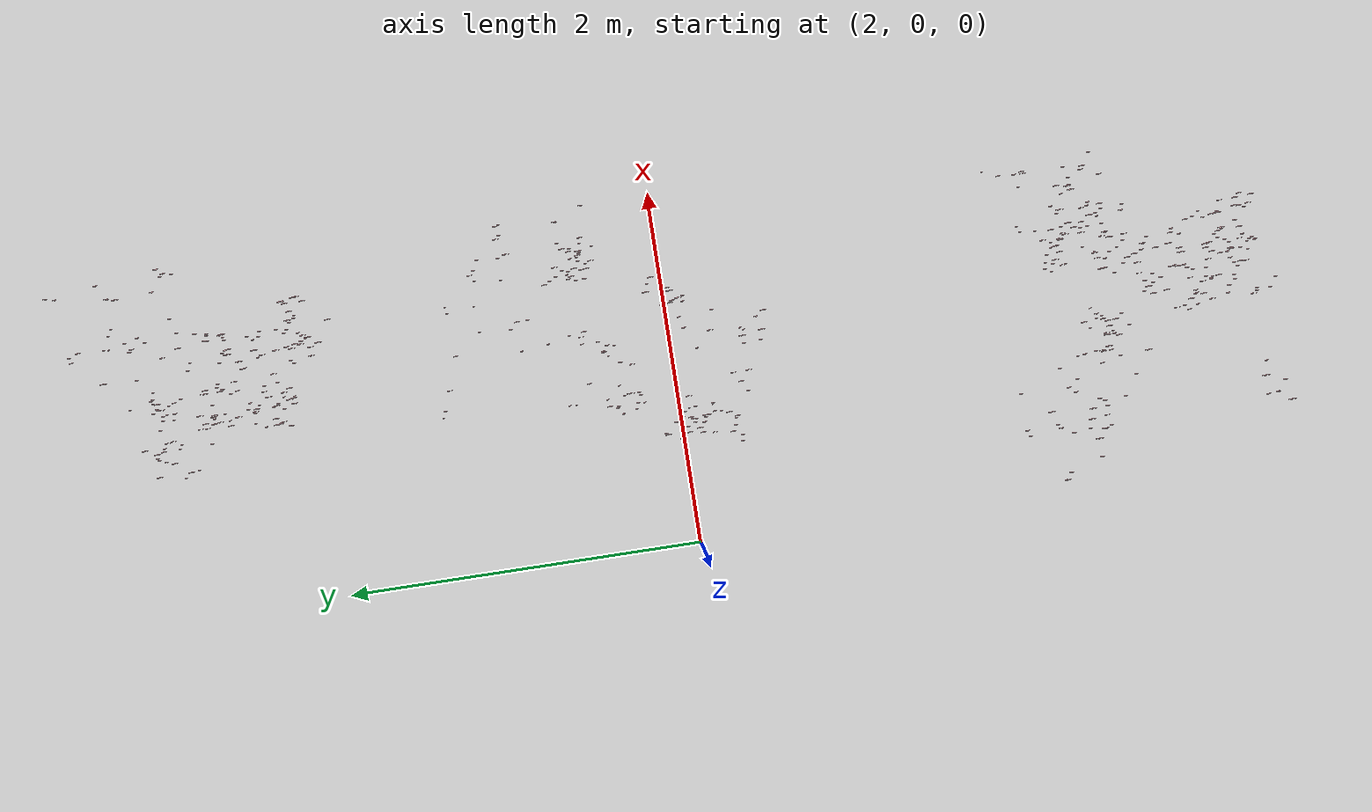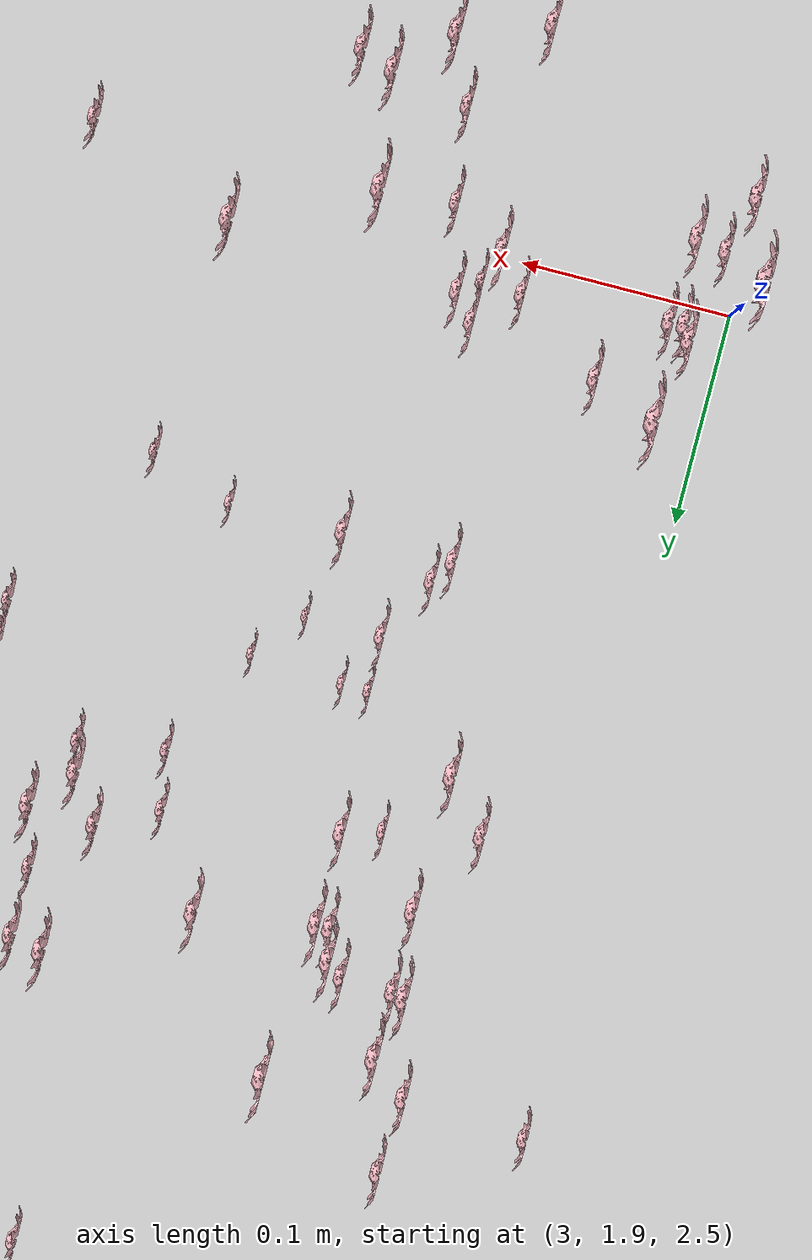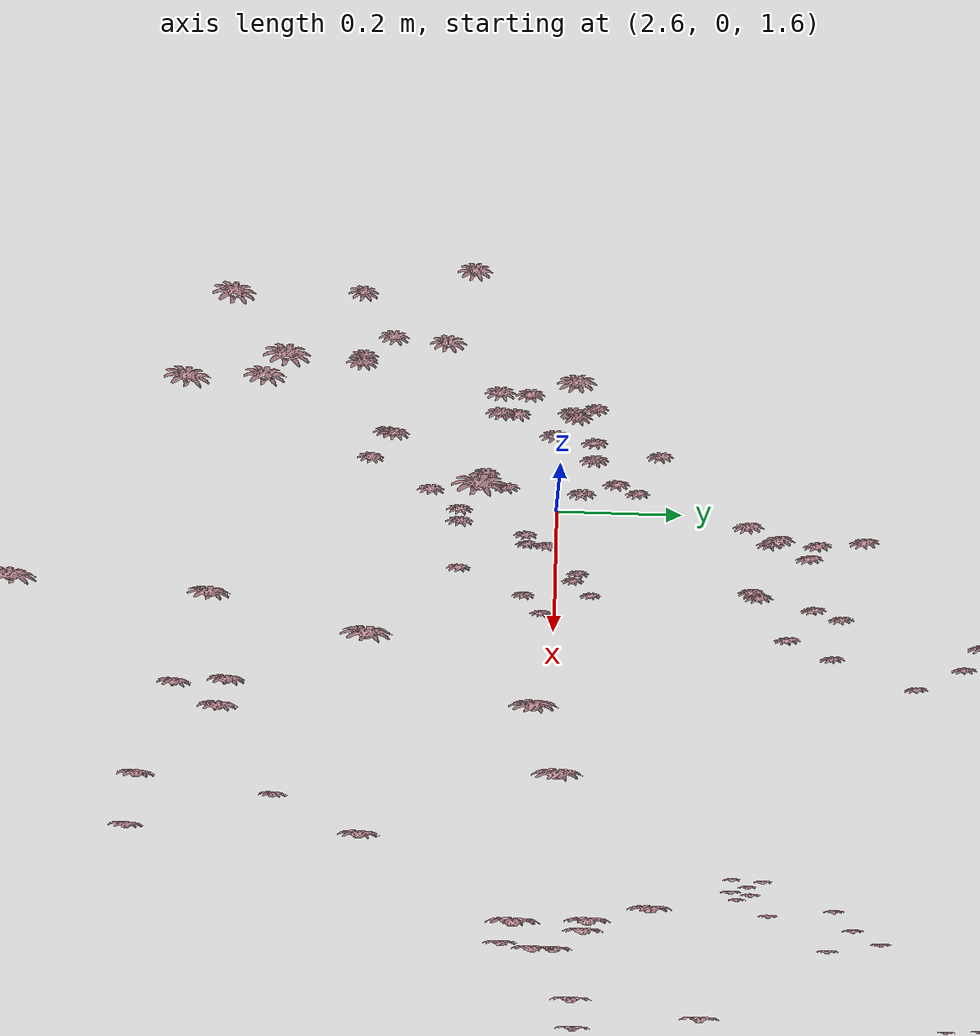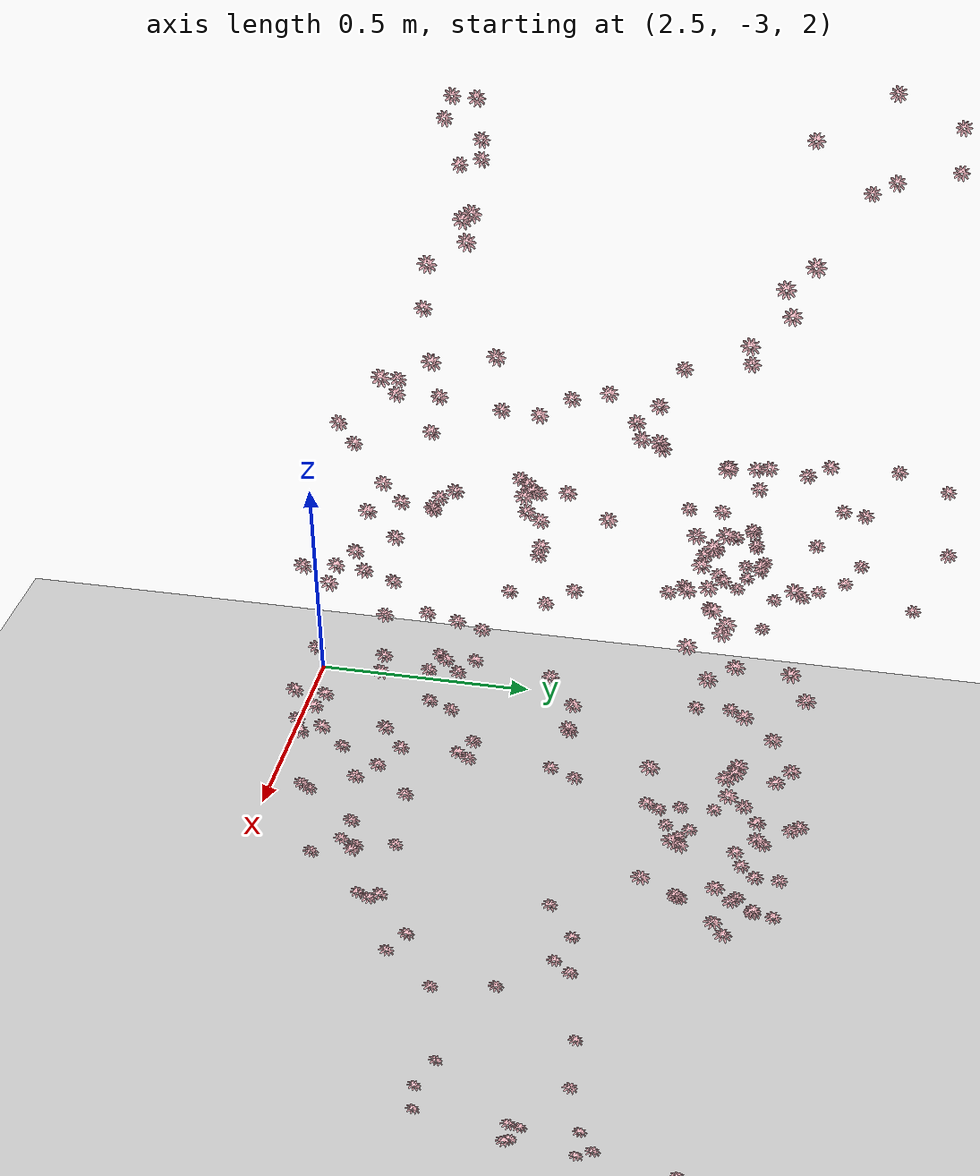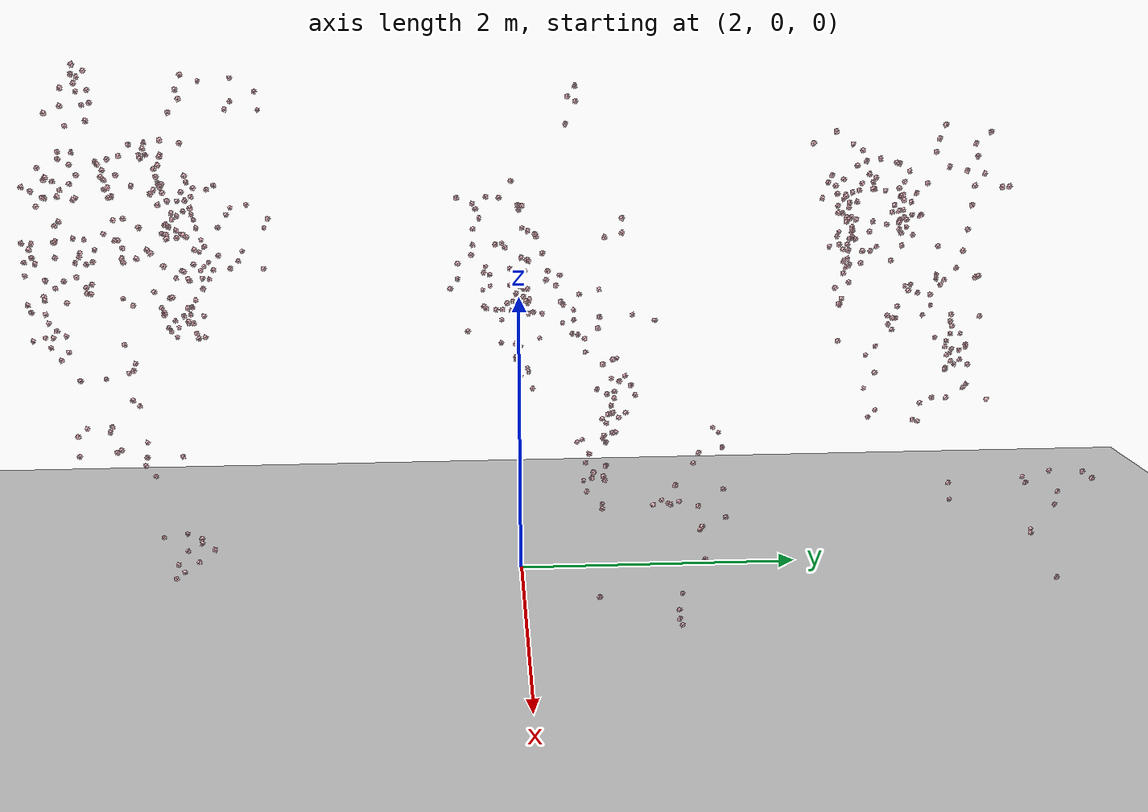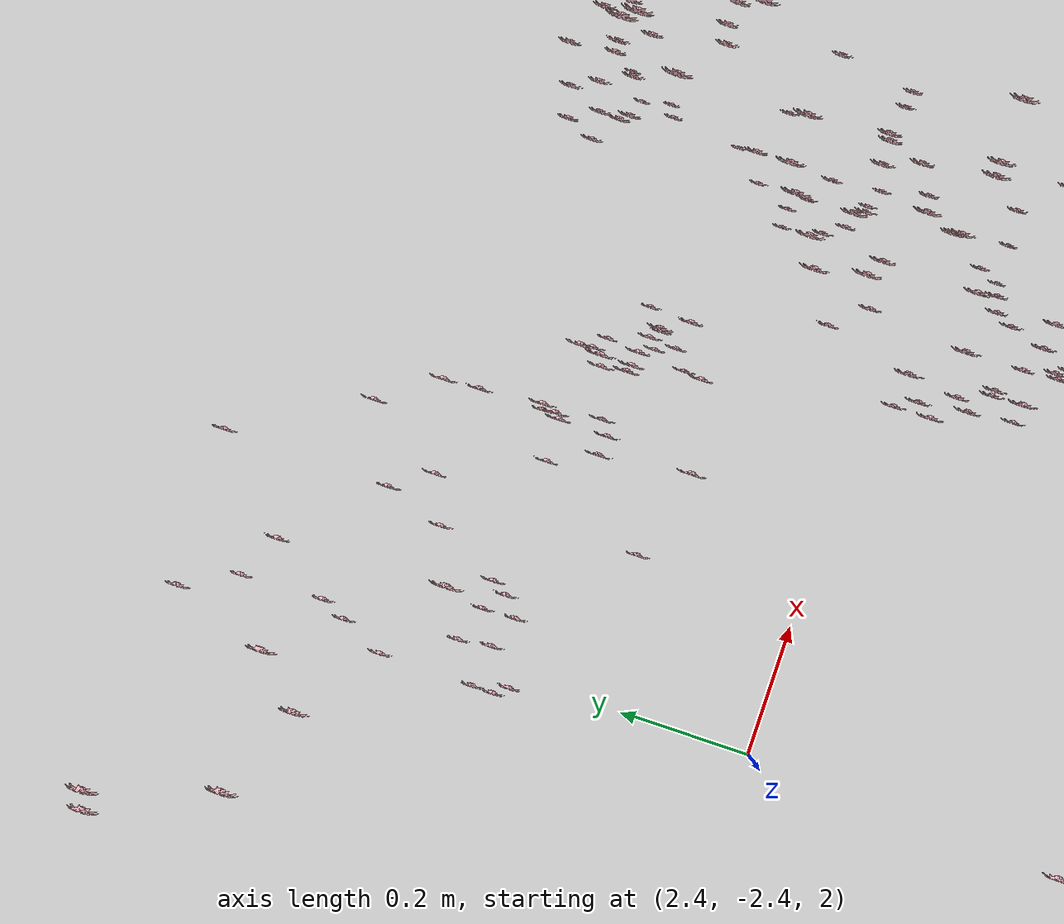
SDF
<?xml version="1.0" ?>
<sdf version="1.4">
  <world name="pollination_world">
    <include>
      <uri>model://ground_plane</uri>
    </include>
    <include>
      <uri>model://sun</uri>
    </include>

    <!-- //__________________________start add targets_________________________// -->

<include>
  <uri>model://flower2</uri>
  <name>target0</name>
  <pose>2.549521332 -2.6100383663 3.5043726089999994 0 -1.57 0</pose>
</include>
<include>
  <uri>model://flower2</uri>
  <name>target1</name>
  <pose>2.4526022340000004 -2.6513044262 3.41545049 0 -1.57 0</pose>
</include>
<include>
  <uri>model://flower2</uri>
  <name>target2</name>
  <pose>2.48974617 -2.5677657604 3.3500640610000003 0 -1.57 0</pose>
</include>
<include>
  <uri>model://flower2</uri>
  <name>target3</name>
  <pose>2.576492767 -2.5472437763 3.4299258169999995 0 -1.57 0</pose>
</include>
<include>
  <uri>model://flower2</uri>
  <name>target4</name>
  <pose>2.6457357019999996 -2.5392674351 3.5434104669999997 0 -1.57 0</pose>
</include>
<include>
  <uri>model://flower2</uri>
  <name>target5</name>
  <pose>2.4932306669999997 -2.6123667812 3.3362809500000004 0 -1.57 0</pose>
</include>
<include>
  <uri>model://flower2</uri>
  <name>target6</name>
  <pose>2.458173065 -1.7410349941 3.352477697 0 -1.57 0</pose>
</include>
<include>
  <uri>model://flower2</uri>
  <name>target7</name>
  <pose>2.5831870649999997 -1.898997364 3.4812798060000008 0 -1.57 0</pose>
</include>
<include>
  <uri>model://flower2</uri>
  <name>target8</name>
  <pose>2.403278351 -1.7882064915 3.300772756 0 -1.57 0</pose>
</include>
<include>
  <uri>model://flower2</uri>
  <name>target9</name>
  <pose>2.331791 -1.7574923037999999 3.484460729 0 -1.57 0</pose>
</include>
<include>
  <uri>model://flower2</uri>
  <name>target10</name>
  <pose>2.278168259 -1.6212519932 3.401232885 0 -1.57 0</pose>
</include>
<include>
  <uri>model://flower2</uri>
  <name>target11</name>
  <pose>2.239747085 -1.6146045208 3.2877012379999995 0 -1.57 0</pose>
</include>
<include>
  <uri>model://flower2</uri>
  <name>target12</name>
  <pose>2.8656402209999996 -1.9499652195 2.9184721119999995 0 -1.57 0</pose>
</include>
<include>
  <uri>model://flower2</uri>
  <name>target13</name>
  <pose>2.9224021149999997 -2.03722019196 2.744812864 0 -1.57 0</pose>
</include>
<include>
  <uri>model://flower2</uri>
  <name>target14</name>
  <pose>2.944951477 -2.07312476635 2.6804163109999997 0 -1.57 0</pose>
</include>
<include>
  <uri>model://flower2</uri>
  <name>target15</name>
  <pose>2.8933526990000002 -2.02477192402 2.59482221 0 -1.57 0</pose>
</include>
<include>
  <uri>model://flower2</uri>
  <name>target16</name>
  <pose>2.884411964 -2.1105987358 2.6179834869999996 0 -1.57 0</pose>
</include>
<include>
  <uri>model://flower2</uri>
  <name>target17</name>
  <pose>2.869206009 -2.01867666721 2.722371648 0 -1.57 0</pose>
</include>
<include>
  <uri>model://flower2</uri>
  <name>target18</name>
  <pose>2.855387077 -1.9829115057 2.74740125 0 -1.57 0</pose>
</include>
<include>
  <uri>model://flower2</uri>
  <name>target19</name>
  <pose>2.778876343 -2.02009230614 2.599551252 0 -1.57 0</pose>
</include>
<include>
  <uri>model://flower2</uri>
  <name>target20</name>
  <pose>2.7972620390000005 -2.0071868372 2.597494024 0 -1.57 0</pose>
</include>
<include>
  <uri>model://flower2</uri>
  <name>target21</name>
  <pose>2.784977188 -1.93171267509 2.636444562 0 -1.57 0</pose>
</include>
<include>
  <uri>model://flower2</uri>
  <name>target22</name>
  <pose>2.85741745 -2.01296843529 2.8070523960000004 0 -1.57 0</pose>
</include>
<include>
  <uri>model://flower2</uri>
  <name>target23</name>
  <pose>2.724957275 -1.95649226189 2.6757228219999996 0 -1.57 0</pose>
</include>
<include>
  <uri>model://flower2</uri>
  <name>target24</name>
  <pose>2.9864676670000003 -2.03337433308 2.074847616 0 -1.57 0</pose>
</include>
<include>
  <uri>model://flower2</uri>
  <name>target25</name>
  <pose>2.932528801 -2.06081737518 2.002407621 0 -1.57 0</pose>
</include>
<include>
  <uri>model://flower2</uri>
  <name>target26</name>
  <pose>2.9418233870000003 -2.0899538672 2.040749772 0 -1.57 0</pose>
</include>
<include>
  <uri>model://flower2</uri>
  <name>target27</name>
  <pose>2.912960281 -2.1100752378 2.057176507 0 -1.57 0</pose>
</include>
<include>
  <uri>model://flower2</uri>
  <name>target28</name>
  <pose>2.955193825 -2.05820277691 2.108008512 0 -1.57 0</pose>
</include>
<include>
  <uri>model://flower2</uri>
  <name>target29</name>
  <pose>2.922577133 -1.98888980389 2.0838160259999996 0 -1.57 0</pose>
</include>
<include>
  <uri>model://flower2</uri>
  <name>target30</name>
  <pose>2.9284782409999996 -2.03843820095 2.363667692 0 -1.57 0</pose>
</include>
<include>
  <uri>model://flower2</uri>
  <name>target31</name>
  <pose>2.892511368 -1.96946307182 2.339554685 0 -1.57 0</pose>
</include>
<include>
  <uri>model://flower2</uri>
  <name>target32</name>
  <pose>2.761917877 -2.1107478929 3.0669386800000003 0 -1.57 0</pose>
</include>
<include>
  <uri>model://flower2</uri>
  <name>target33</name>
  <pose>2.648920936 -2.1002643931 2.6682703909999996 0 -1.57 0</pose>
</include>
<include>
  <uri>model://flower2</uri>
  <name>target34</name>
  <pose>2.751149826 -2.01142974854 2.844952062 0 -1.57 0</pose>
</include>
<include>
  <uri>model://flower2</uri>
  <name>target35</name>
  <pose>2.7834492109999998 -1.94749645233 2.8209288910000003 0 -1.57 0</pose>
</include>
<include>
  <uri>model://flower2</uri>
  <name>target36</name>
  <pose>2.78791748 -1.92989189148 2.8745277529999997 0 -1.57 0</pose>
</include>
<include>
  <uri>model://flower2</uri>
  <name>target37</name>
  <pose>2.781592903 -1.8538425255 2.8621954090000004 0 -1.57 0</pose>
</include>
<include>
  <uri>model://flower2</uri>
  <name>target38</name>
  <pose>2.7788475420000003 -1.8110141754 2.8858139549999997 0 -1.57 0</pose>
</include>
<include>
  <uri>model://flower2</uri>
  <name>target39</name>
  <pose>2.730893516 -1.7333572865 2.747415021 0 -1.57 0</pose>
</include>
<include>
  <uri>model://flower2</uri>
  <name>target40</name>
  <pose>2.4314376069999994 -1.5634729481 2.6339646279999998 0 -1.57 0</pose>
</include>
<include>
  <uri>model://flower2</uri>
  <name>target41</name>
  <pose>2.532847595 -1.6731767368 2.736160787 0 -1.57 0</pose>
</include>
<include>
  <uri>model://flower2</uri>
  <name>target42</name>
  <pose>2.636111679 -1.5553819561 2.6086382799999996 0 -1.57 0</pose>
</include>
<include>
  <uri>model://flower2</uri>
  <name>target43</name>
  <pose>2.4451196289999997 -1.6076370716000001 2.3199423340000003 0 -1.57 0</pose>
</include>
<include>
  <uri>model://flower2</uri>
  <name>target44</name>
  <pose>2.7788144299999997 -1.95446043015 2.717726644 0 -1.57 0</pose>
</include>
<include>
  <uri>model://flower2</uri>
  <name>target45</name>
  <pose>2.633951187 -1.7795350266 2.690334943 0 -1.57 0</pose>
</include>
<include>
  <uri>model://flower2</uri>
  <name>target46</name>
  <pose>2.665770988 -1.8278544331 2.61880338 0 -1.57 0</pose>
</include>
<include>
  <uri>model://flower2</uri>
  <name>target47</name>
  <pose>2.598824081 -1.8503673267 2.435369466 0 -1.57 0</pose>
</include>
<include>
  <uri>model://flower2</uri>
  <name>target48</name>
  <pose>2.553562889 -1.94004546165 2.484448484 0 -1.57 0</pose>
</include>
<include>
  <uri>model://flower2</uri>
  <name>target49</name>
  <pose>2.4696144870000003 -1.96546011925 2.4650744369999997 0 -1.57 0</pose>
</include>
<include>
  <uri>model://flower2</uri>
  <name>target50</name>
  <pose>2.5427964019999996 -1.96123268127 2.522735303 0 -1.57 0</pose>
</include>
<include>
  <uri>model://flower2</uri>
  <name>target51</name>
  <pose>2.512806854 -1.98308084965 2.442297223 0 -1.57 0</pose>
</include>
<include>
  <uri>model://flower2</uri>
  <name>target52</name>
  <pose>2.402539902 -1.95665551186 2.355714467 0 -1.57 0</pose>
</include>
<include>
  <uri>model://flower2</uri>
  <name>target53</name>
  <pose>2.3994944 -1.98711070061 2.3300126009999995 0 -1.57 0</pose>
</include>
<include>
  <uri>model://flower2</uri>
  <name>target54</name>
  <pose>2.411036377 -2.00719582558 2.306699651 0 -1.57 0</pose>
</include>
<include>
  <uri>model://flower2</uri>
  <name>target55</name>
  <pose>2.501446304 -1.93782556534 2.267766012 0 -1.57 0</pose>
</include>
<include>
  <uri>model://flower2</uri>
  <name>target56</name>
  <pose>2.4534198 -1.9184611225100001 2.3164672599999996 0 -1.57 0</pose>
</include>
<include>
  <uri>model://flower2</uri>
  <name>target57</name>
  <pose>2.4012767030000006 -1.82273139 2.3145312630000006 0 -1.57 0</pose>
</include>
<include>
  <uri>model://flower2</uri>
  <name>target58</name>
  <pose>2.4350077060000004 -1.7637109469999999 2.3684723030000003 0 -1.57 0</pose>
</include>
<include>
  <uri>model://flower2</uri>
  <name>target59</name>
  <pose>2.4566383359999997 -1.7320695972 2.435418332 0 -1.57 0</pose>
</include>
<include>
  <uri>model://flower2</uri>
  <name>target60</name>
  <pose>2.92980648 -2.3552958107 2.589889539 0 -1.57 0</pose>
</include>
<include>
  <uri>model://flower2</uri>
  <name>target61</name>
  <pose>2.96274559 -2.4228843403 2.6341686380000002 0 -1.57 0</pose>
</include>
<include>
  <uri>model://flower2</uri>
  <name>target62</name>
  <pose>2.937017059 -2.368262701 2.711718915 0 -1.57 0</pose>
</include>
<include>
  <uri>model://flower2</uri>
  <name>target63</name>
  <pose>2.915329742 -2.3704406643 2.845369619 0 -1.57 0</pose>
</include>
<include>
  <uri>model://flower2</uri>
  <name>target64</name>
  <pose>2.933321533 -2.4043152428 2.88662824 0 -1.57 0</pose>
</include>
<include>
  <uri>model://flower2</uri>
  <name>target65</name>
  <pose>2.940034485 -2.3012907504999998 3.081480535 0 -1.57 0</pose>
</include>
<include>
  <uri>model://flower2</uri>
  <name>target66</name>
  <pose>2.984067154 -2.3556797266 3.065626806 0 -1.57 0</pose>
</include>
<include>
  <uri>model://flower2</uri>
  <name>target67</name>
  <pose>2.949601211 -2.4359159756 3.047976888 0 -1.57 0</pose>
</include>
<include>
  <uri>model://flower2</uri>
  <name>target68</name>
  <pose>3.0166530608 -2.1662891412 3.089405797 0 -1.57 0</pose>
</include>
<include>
  <uri>model://flower2</uri>
  <name>target69</name>
  <pose>3.0511716842 -2.1517394353 3.076197942 0 -1.57 0</pose>
</include>
<include>
  <uri>model://flower2</uri>
  <name>target70</name>
  <pose>3.0226766967 -2.2176823747 3.1492910510000005 0 -1.57 0</pose>
</include>
<include>
  <uri>model://flower2</uri>
  <name>target71</name>
  <pose>3.0797096633 -2.1169371939 3.1664217889999997 0 -1.57 0</pose>
</include>
<include>
  <uri>model://flower2</uri>
  <name>target72</name>
  <pose>3.1174854659 -2.1048917866 3.102195638 0 -1.57 0</pose>
</include>
<include>
  <uri>model://flower2</uri>
  <name>target73</name>
  <pose>3.1665442656 -2.1043423772 3.143556188 0 -1.57 0</pose>
</include>
<include>
  <uri>model://flower2</uri>
  <name>target74</name>
  <pose>2.8523917770000002 -1.97313286781 3.1413896689999996 0 -1.57 0</pose>
</include>
<include>
  <uri>model://flower2</uri>
  <name>target75</name>
  <pose>3.1359710692 -1.95651994705 3.3348539480000006 0 -1.57 0</pose>
</include>
<include>
  <uri>model://flower2</uri>
  <name>target76</name>
  <pose>3.1611017989 -1.8871506119 3.4111956529999996 0 -1.57 0</pose>
</include>
<include>
  <uri>model://flower2</uri>
  <name>target77</name>
  <pose>3.1624626159 -1.90097389221 3.46167188 0 -1.57 0</pose>
</include>
<include>
  <uri>model://flower2</uri>
  <name>target78</name>
  <pose>3.234345703 -1.8513806725 3.5426421860000006 0 -1.57 0</pose>
</include>
<include>
  <uri>model://flower2</uri>
  <name>target79</name>
  <pose>2.946264725 -2.5824401951000002 3.249695943 0 -1.57 0</pose>
</include>
<include>
  <uri>model://flower2</uri>
  <name>target80</name>
  <pose>2.969157295 -2.6315427494 3.1063856249999997 0 -1.57 0</pose>
</include>
<include>
  <uri>model://flower2</uri>
  <name>target81</name>
  <pose>2.957395096 -2.639490099 3.0664088950000004 0 -1.57 0</pose>
</include>
<include>
  <uri>model://flower2</uri>
  <name>target82</name>
  <pose>3.0078963088 -2.742678442 3.0216536460000003 0 -1.57 0</pose>
</include>
<include>
  <uri>model://flower2</uri>
  <name>target83</name>
  <pose>2.962771416 -2.7288124943 2.9500086719999996 0 -1.57 0</pose>
</include>
<include>
  <uri>model://flower2</uri>
  <name>target84</name>
  <pose>2.999331093 -2.5643732738000002 2.8390551119999996 0 -1.57 0</pose>
</include>
<include>
  <uri>model://flower2</uri>
  <name>target85</name>
  <pose>2.964072647 -2.5596122265 2.84440038 0 -1.57 0</pose>
</include>
<include>
  <uri>model://flower2</uri>
  <name>target86</name>
  <pose>3.0245598601 -2.5380475903 3.109841588 0 -1.57 0</pose>
</include>
<include>
  <uri>model://flower2</uri>
  <name>target87</name>
  <pose>3.1073965453 -2.2021615386 2.928448308 0 -1.57 0</pose>
</include>
<include>
  <uri>model://flower2</uri>
  <name>target88</name>
  <pose>3.085121498 -2.2696385431 2.7424866230000005 0 -1.57 0</pose>
</include>
<include>
  <uri>model://flower2</uri>
  <name>target89</name>
  <pose>3.1289533996 -2.3258605003 2.867732671 0 -1.57 0</pose>
</include>
<include>
  <uri>model://flower2</uri>
  <name>target90</name>
  <pose>3.0614910888 -2.3621080112 2.95945516 0 -1.57 0</pose>
</include>
<include>
  <uri>model://flower2</uri>
  <name>target91</name>
  <pose>3.1268664931 -2.2755958939 2.99164266 0 -1.57 0</pose>
</include>
<include>
  <uri>model://flower2</uri>
  <name>target92</name>
  <pose>3.1240823363 -2.3279992056 2.922595266 0 -1.57 0</pose>
</include>
<include>
  <uri>model://flower2</uri>
  <name>target93</name>
  <pose>3.1846649932 -2.3318550587 3.0268434650000002 0 -1.57 0</pose>
</include>
<include>
  <uri>model://flower2</uri>
  <name>target94</name>
  <pose>3.2060542296 -2.3363899279 2.9938358819999995 0 -1.57 0</pose>
</include>
<include>
  <uri>model://flower2</uri>
  <name>target95</name>
  <pose>3.2684602735999997 -2.329446249 3.067916921 0 -1.57 0</pose>
</include>
<include>
  <uri>model://flower2</uri>
  <name>target96</name>
  <pose>3.0450171279 -2.5511547756 3.0435331469999998 0 -1.57 0</pose>
</include>
<include>
  <uri>model://flower2</uri>
  <name>target97</name>
  <pose>3.0571845243999998 -2.5099929428 2.616803602 0 -1.57 0</pose>
</include>
<include>
  <uri>model://flower2</uri>
  <name>target98</name>
  <pose>3.0540183639 -2.5712666416 2.6258838399999997 0 -1.57 0</pose>
</include>
<include>
  <uri>model://flower2</uri>
  <name>target99</name>
  <pose>3.0521397399 -2.5745400715 2.481690038 0 -1.57 0</pose>
</include>
<include>
  <uri>model://flower2</uri>
  <name>target100</name>
  <pose>3.035302925 -2.5177061367 2.470961164 0 -1.57 0</pose>
</include>
<include>
  <uri>model://flower2</uri>
  <name>target101</name>
  <pose>2.984918823 -2.4766285992 2.546981939 0 -1.57 0</pose>
</include>
<include>
  <uri>model://flower2</uri>
  <name>target102</name>
  <pose>3.0666238021 -2.3200608158 2.272608312 0 -1.57 0</pose>
</include>
<include>
  <uri>model://flower2</uri>
  <name>target103</name>
  <pose>3.0306365584 -2.2760041809000002 2.220984338 0 -1.57 0</pose>
</include>
<include>
  <uri>model://flower2</uri>
  <name>target104</name>
  <pose>3.1006069564 -2.5082186794 2.312733472 0 -1.57 0</pose>
</include>
<include>
  <uri>model://flower2</uri>
  <name>target105</name>
  <pose>3.1130089568 -2.4837912655 2.3113477450000004 0 -1.57 0</pose>
</include>
<include>
  <uri>model://flower2</uri>
  <name>target106</name>
  <pose>3.1282336806 -2.4682352161 2.370935567 0 -1.57 0</pose>
</include>
<include>
  <uri>model://flower2</uri>
  <name>target107</name>
  <pose>2.975450478 -2.5503727627 2.3208079660000003 0 -1.57 0</pose>
</include>
<include>
  <uri>model://flower2</uri>
  <name>target108</name>
  <pose>3.0447480391 -2.5773625851 2.395742162 0 -1.57 0</pose>
</include>
<include>
  <uri>model://flower2</uri>
  <name>target109</name>
  <pose>2.997722473 -2.4892145157 2.476632016 0 -1.57 0</pose>
</include>
<include>
  <uri>model://flower2</uri>
  <name>target110</name>
  <pose>3.0980089568 -2.5264178371 2.548682607 0 -1.57 0</pose>
</include>
<include>
  <uri>model://flower2</uri>
  <name>target111</name>
  <pose>3.0408000945 -2.5518632793 2.514591039 0 -1.57 0</pose>
</include>
<include>
  <uri>model://flower2</uri>
  <name>target112</name>
  <pose>3.2170500563999997 -2.618214674 2.6363095600000004 0 -1.57 0</pose>
</include>
<include>
  <uri>model://flower2</uri>
  <name>target113</name>
  <pose>3.2006198882 -2.6164935398 2.7219899110000005 0 -1.57 0</pose>
</include>
<include>
  <uri>model://flower2</uri>
  <name>target114</name>
  <pose>3.1018686675 -2.6249128246 2.730612462 0 -1.57 0</pose>
</include>
<include>
  <uri>model://flower2</uri>
  <name>target115</name>
  <pose>3.1024277495 -2.6337061024 2.9569251000000003 0 -1.57 0</pose>
</include>
<include>
  <uri>model://flower2</uri>
  <name>target116</name>
  <pose>3.0828604125 -2.605521574 2.9051807910000003 0 -1.57 0</pose>
</include>
<include>
  <uri>model://flower2</uri>
  <name>target117</name>
  <pose>3.1679735564000002 -2.479083643 2.998190587 0 -1.57 0</pose>
</include>
<include>
  <uri>model://flower2</uri>
  <name>target118</name>
  <pose>3.1548697661 -2.5260603046 2.948244985 0 -1.57 0</pose>
</include>
<include>
  <uri>model://flower2</uri>
  <name>target119</name>
  <pose>3.1668297576 -2.5976520634 2.880707448000001 0 -1.57 0</pose>
</include>
<include>
  <uri>model://flower2</uri>
  <name>target120</name>
  <pose>3.2263615798 -2.6584503078 2.8822092180000003 0 -1.57 0</pose>
</include>
<include>
  <uri>model://flower2</uri>
  <name>target121</name>
  <pose>3.2075571822 -2.7047593784 2.831951688 0 -1.57 0</pose>
</include>
<include>
  <uri>model://flower2</uri>
  <name>target122</name>
  <pose>3.2618834304 -2.6196843624 2.998849233 0 -1.57 0</pose>
</include>
<include>
  <uri>model://flower2</uri>
  <name>target123</name>
  <pose>3.2955051612 -2.623147459 2.890295614 0 -1.57 0</pose>
</include>
<include>
  <uri>model://flower2</uri>
  <name>target124</name>
  <pose>3.2691616439 -2.6113039303 2.638598493 0 -1.57 0</pose>
</include>
<include>
  <uri>model://flower2</uri>
  <name>target125</name>
  <pose>3.3467585563 -2.586449461 2.567226423 0 -1.57 0</pose>
</include>
<include>
  <uri>model://flower2</uri>
  <name>target126</name>
  <pose>3.1951845931 -2.7604252529 2.61996507 0 -1.57 0</pose>
</include>
<include>
  <uri>model://flower2</uri>
  <name>target127</name>
  <pose>3.2009349059 -2.8130624866 2.438844922 0 -1.57 0</pose>
</include>
<include>
  <uri>model://flower2</uri>
  <name>target128</name>
  <pose>3.1944110106 -2.7510570621 2.505548108 0 -1.57 0</pose>
</include>
<include>
  <uri>model://flower2</uri>
  <name>target129</name>
  <pose>3.2077281951 -2.813424902 2.2720143250000002 0 -1.57 0</pose>
</include>
<include>
  <uri>model://flower2</uri>
  <name>target130</name>
  <pose>3.1062873458 -2.753141489 2.297730001 0 -1.57 0</pose>
</include>
<include>
  <uri>model://flower2</uri>
  <name>target131</name>
  <pose>3.1580419539 -2.8166170788 2.21687074 0 -1.57 0</pose>
</include>
<include>
  <uri>model://flower2</uri>
  <name>target132</name>
  <pose>3.1733554458 -2.8195316601 2.050997938 0 -1.57 0</pose>
</include>
<include>
  <uri>model://flower2</uri>
  <name>target133</name>
  <pose>3.1294456099 -2.7636666203 2.057740415 0 -1.57 0</pose>
</include>
<include>
  <uri>model://flower2</uri>
  <name>target134</name>
  <pose>3.4162794684 -2.6530593204 2.9429238639999995 0 -1.57 0</pose>
</include>
<include>
  <uri>model://flower2</uri>
  <name>target135</name>
  <pose>3.4036842536 -2.7026430225 2.965326284 0 -1.57 0</pose>
</include>
<include>
  <uri>model://flower2</uri>
  <name>target136</name>
  <pose>3.3674794959 -2.7158094692 2.6178559999999997 0 -1.57 0</pose>
</include>
<include>
  <uri>model://flower2</uri>
  <name>target137</name>
  <pose>3.3713523673 -2.7507820605999997 2.653888372 0 -1.57 0</pose>
</include>
<include>
  <uri>model://flower2</uri>
  <name>target138</name>
  <pose>3.3710989379000003 -2.7036419773 2.571837018 0 -1.57 0</pose>
</include>
<include>
  <uri>model://flower2</uri>
  <name>target139</name>
  <pose>3.3584927939 -2.7518433857 2.543615239 0 -1.57 0</pose>
</include>
<include>
  <uri>model://flower2</uri>
  <name>target140</name>
  <pose>3.3536939048 -2.6506654453 2.4403673680000004 0 -1.57 0</pose>
</include>
<include>
  <uri>model://flower2</uri>
  <name>target141</name>
  <pose>3.3614183997 -2.6631878948 2.331619886 0 -1.57 0</pose>
</include>
<include>
  <uri>model://flower2</uri>
  <name>target142</name>
  <pose>3.3562192534 -2.6691422176 2.248807958 0 -1.57 0</pose>
</include>
<include>
  <uri>model://flower2</uri>
  <name>target143</name>
  <pose>3.2689839553 -2.6886314487 2.177755063 0 -1.57 0</pose>
</include>
<include>
  <uri>model://flower2</uri>
  <name>target144</name>
  <pose>3.2579371261 -2.6947021008 2.032480081 0 -1.57 0</pose>
</include>
<include>
  <uri>model://flower2</uri>
  <name>target145</name>
  <pose>3.234035797 -2.6404874706 2.3710198719999998 0 -1.57 0</pose>
</include>
<include>
  <uri>model://flower2</uri>
  <name>target146</name>
  <pose>3.2156611632 -2.5953907681 2.407735723 0 -1.57 0</pose>
</include>
<include>
  <uri>model://flower2</uri>
  <name>target147</name>
  <pose>3.2128270339 -2.5928998852 2.282698377 0 -1.57 0</pose>
</include>
<include>
  <uri>model://flower2</uri>
  <name>target148</name>
  <pose>3.3801029204 -2.6098505306 2.1593808109999997 0 -1.57 0</pose>
</include>
<include>
  <uri>model://flower2</uri>
  <name>target149</name>
  <pose>3.3470526313 -2.6446059704 2.111467145 0 -1.57 0</pose>
</include>
<include>
  <uri>model://flower2</uri>
  <name>target150</name>
  <pose>3.1387546538 -2.6419435406 2.068736547 0 -1.57 0</pose>
</include>
<include>
  <uri>model://flower2</uri>
  <name>target151</name>
  <pose>3.2578015899 -2.2413021255 2.599980024 0 -1.57 0</pose>
</include>
<include>
  <uri>model://flower2</uri>
  <name>target152</name>
  <pose>3.2286214446 -2.2891338539 2.638677915 0 -1.57 0</pose>
</include>
<include>
  <uri>model://flower2</uri>
  <name>target153</name>
  <pose>3.2296722411000003 -2.2522825336 2.5128164799999997 0 -1.57 0</pose>
</include>
<include>
  <uri>model://flower2</uri>
  <name>target154</name>
  <pose>3.2576174926 -2.2501822519 2.5431373340000003 0 -1.57 0</pose>
</include>
<include>
  <uri>model://flower2</uri>
  <name>target155</name>
  <pose>3.3069233512 -2.02897742748 2.9304108170000003 0 -1.57 0</pose>
</include>
<include>
  <uri>model://flower2</uri>
  <name>target156</name>
  <pose>3.314286766 -1.99054491997 2.9458464560000004 0 -1.57 0</pose>
</include>
<include>
  <uri>model://flower2</uri>
  <name>target157</name>
  <pose>3.3310964393 -2.00304611206 3.004687169 0 -1.57 0</pose>
</include>
<include>
  <uri>model://flower2</uri>
  <name>target158</name>
  <pose>3.3047442435 -2.0168953228 3.0472116600000003 0 -1.57 0</pose>
</include>
<include>
  <uri>model://flower2</uri>
  <name>target159</name>
  <pose>3.3980417632 -1.8364106369 3.017501043 0 -1.57 0</pose>
</include>
<include>
  <uri>model://flower2</uri>
  <name>target160</name>
  <pose>3.425315132 -1.97122990608 2.9799197129999997 0 -1.57 0</pose>
</include>
<include>
  <uri>model://flower2</uri>
  <name>target161</name>
  <pose>3.3708995627 -1.97926757812 3.071923726 0 -1.57 0</pose>
</include>
<include>
  <uri>model://flower2</uri>
  <name>target162</name>
  <pose>3.4053411483 -1.95628465652 3.122162069 0 -1.57 0</pose>
</include>
<include>
  <uri>model://flower2</uri>
  <name>target163</name>
  <pose>3.3255492209 -1.96748402596 3.2023586780000004 0 -1.57 0</pose>
</include>
<include>
  <uri>model://flower2</uri>
  <name>target164</name>
  <pose>3.1857118224 -2.3928309441 3.2971252189999998 0 -1.57 0</pose>
</include>
<include>
  <uri>model://flower2</uri>
  <name>target165</name>
  <pose>3.166641426 -2.4514302731 3.543783315 0 -1.57 0</pose>
</include>
<include>
  <uri>model://flower2</uri>
  <name>target166</name>
  <pose>3.1516353988 -2.4483093070999997 3.4954168450000003 0 -1.57 0</pose>
</include>
<include>
  <uri>model://flower2</uri>
  <name>target167</name>
  <pose>3.2027570723 -2.5064601517 3.473900655 0 -1.57 0</pose>
</include>
<include>
  <uri>model://flower2</uri>
  <name>target168</name>
  <pose>3.2599114226 -2.4136155987 3.600824331 0 -1.57 0</pose>
</include>
<include>
  <uri>model://flower2</uri>
  <name>target169</name>
  <pose>3.2164653014 -2.09857562304 2.340604871 0 -1.57 0</pose>
</include>
<include>
  <uri>model://flower2</uri>
  <name>target170</name>
  <pose>3.2216115188 -1.9179100132 2.243957151 0 -1.57 0</pose>
</include>
<include>
  <uri>model://flower2</uri>
  <name>target171</name>
  <pose>3.2172832869 -1.90473205566 2.205064805 0 -1.57 0</pose>
</include>
<include>
  <uri>model://flower2</uri>
  <name>target172</name>
  <pose>3.2470111846 -1.8635133171 2.296065687 0 -1.57 0</pose>
</include>
<include>
  <uri>model://flower2</uri>
  <name>target173</name>
  <pose>3.2324110793 -1.8747312164 2.096548856 0 -1.57 0</pose>
</include>
<include>
  <uri>model://flower2</uri>
  <name>target174</name>
  <pose>3.2843018722 -1.90477388382 2.1817662180000004 0 -1.57 0</pose>
</include>
<include>
  <uri>model://flower2</uri>
  <name>target175</name>
  <pose>3.3125617026 -1.8700992393 2.268376478 0 -1.57 0</pose>
</include>
<include>
  <uri>model://flower2</uri>
  <name>target176</name>
  <pose>3.2123870467 -1.8324950027 2.069783529 0 -1.57 0</pose>
</include>
<include>
  <uri>model://flower2</uri>
  <name>target177</name>
  <pose>3.241551094 -1.8247735023 2.200730623 0 -1.57 0</pose>
</include>
<include>
  <uri>model://flower2</uri>
  <name>target178</name>
  <pose>3.2754611586999998 -1.8104053783 2.3673368959999994 0 -1.57 0</pose>
</include>
<include>
  <uri>model://flower2</uri>
  <name>target179</name>
  <pose>3.1953487395 -1.8749142933 2.057505506 0 -1.57 0</pose>
</include>
<include>
  <uri>model://flower2</uri>
  <name>target180</name>
  <pose>3.3101269911999998 -1.8698733330000001 2.177620004 0 -1.57 0</pose>
</include>
<include>
  <uri>model://flower2</uri>
  <name>target181</name>
  <pose>3.3422786902 -1.91256663322 2.2251604780000003 0 -1.57 0</pose>
</include>
<include>
  <uri>model://flower2</uri>
  <name>target182</name>
  <pose>3.3429301833 -1.8728007317 2.43677873 0 -1.57 0</pose>
</include>
<include>
  <uri>model://flower2</uri>
  <name>target183</name>
  <pose>3.3584998511 -1.8983684349 2.487747281 0 -1.57 0</pose>
</include>
<include>
  <uri>model://flower2</uri>
  <name>target184</name>
  <pose>3.312059574 -1.8446929169 2.515082029 0 -1.57 0</pose>
</include>
<include>
  <uri>model://flower2</uri>
  <name>target185</name>
  <pose>3.3465704726 -1.7925701046 2.441538747 0 -1.57 0</pose>
</include>
<include>
  <uri>model://flower2</uri>
  <name>target186</name>
  <pose>3.4625881576 -1.8651947689 2.503890165 0 -1.57 0</pose>
</include>
<include>
  <uri>model://flower2</uri>
  <name>target187</name>
  <pose>3.3878068541 -1.8153350925 2.610989545 0 -1.57 0</pose>
</include>
<include>
  <uri>model://flower2</uri>
  <name>target188</name>
  <pose>3.5573359488 -1.9282100296 2.376563466 0 -1.57 0</pose>
</include>
<include>
  <uri>model://flower2</uri>
  <name>target189</name>
  <pose>3.599771881 -1.90511335373 2.389921926 0 -1.57 0</pose>
</include>
<include>
  <uri>model://flower2</uri>
  <name>target190</name>
  <pose>3.6765918826 -1.91871447563 2.575996106 0 -1.57 0</pose>
</include>
<include>
  <uri>model://flower2</uri>
  <name>target191</name>
  <pose>3.6496944617000002 -1.98719900608 2.640301259 0 -1.57 0</pose>
</include>
<include>
  <uri>model://flower2</uri>
  <name>target192</name>
  <pose>3.7264015005999997 -2.04182896614 2.6270360310000003 0 -1.57 0</pose>
</include>
<include>
  <uri>model://flower2</uri>
  <name>target193</name>
  <pose>3.6655346965 -1.99905983448 2.6629850130000006 0 -1.57 0</pose>
</include>
<include>
  <uri>model://flower2</uri>
  <name>target194</name>
  <pose>3.610195999 -2.04683218002 2.7724348199999995 0 -1.57 0</pose>
</include>
<include>
  <uri>model://flower2</uri>
  <name>target195</name>
  <pose>3.5765730475 -1.8993901539 2.768069433 0 -1.57 0</pose>
</include>
<include>
  <uri>model://flower2</uri>
  <name>target196</name>
  <pose>3.5592635344 -1.92047207832 2.7241516619999997 0 -1.57 0</pose>
</include>
<include>
  <uri>model://flower2</uri>
  <name>target197</name>
  <pose>3.5839507674 -1.91293306351 2.705662587 0 -1.57 0</pose>
</include>
<include>
  <uri>model://flower2</uri>
  <name>target198</name>
  <pose>3.6147224616 -1.90193059921 2.785626577 0 -1.57 0</pose>
</include>
<include>
  <uri>model://flower2</uri>
  <name>target199</name>
  <pose>3.393052864 -1.8527765369 2.6833501940000004 0 -1.57 0</pose>
</include>
<include>
  <uri>model://flower2</uri>
  <name>target200</name>
  <pose>3.3810802459 -1.9077370739 2.7187951410000006 0 -1.57 0</pose>
</include>
<include>
  <uri>model://flower2</uri>
  <name>target201</name>
  <pose>3.4896243857 -1.7976430607 2.857004445 0 -1.57 0</pose>
</include>
<include>
  <uri>model://flower2</uri>
  <name>target202</name>
  <pose>3.4598015403 -1.92346650124 2.8899907810000003 0 -1.57 0</pose>
</include>
<include>
  <uri>model://flower2</uri>
  <name>target203</name>
  <pose>3.42176445 -1.95359241486 2.929988988 0 -1.57 0</pose>
</include>
<include>
  <uri>model://flower2</uri>
  <name>target204</name>
  <pose>3.4830734443 -1.96815102577 2.874658025 0 -1.57 0</pose>
</include>
<include>
  <uri>model://flower2</uri>
  <name>target205</name>
  <pose>3.4642941282999997 -1.9433125782 2.9815695699999996 0 -1.57 0</pose>
</include>
<include>
  <uri>model://flower2</uri>
  <name>target206</name>
  <pose>3.4676146316 -2.00748848915 2.929257711 0 -1.57 0</pose>
</include>
<include>
  <uri>model://flower2</uri>
  <name>target207</name>
  <pose>3.4667594146 -1.8278912449 2.892590955 0 -1.57 0</pose>
</include>
<include>
  <uri>model://flower2</uri>
  <name>target208</name>
  <pose>3.3853893851 -2.4588888168 3.390882085 0 -1.57 0</pose>
</include>
<include>
  <uri>model://flower2</uri>
  <name>target209</name>
  <pose>3.3888111686 -2.5450524235 3.3540376789999993 0 -1.57 0</pose>
</include>
<include>
  <uri>model://flower2</uri>
  <name>target210</name>
  <pose>3.3605332374 -2.01613725662 2.23731109 0 -1.57 0</pose>
</include>
<include>
  <uri>model://flower2</uri>
  <name>target211</name>
  <pose>3.3838241958 -2.00850976467 2.2578322159999997 0 -1.57 0</pose>
</include>
<include>
  <uri>model://flower2</uri>
  <name>target212</name>
  <pose>3.4114264106 -2.01443712234 2.291733259 0 -1.57 0</pose>
</include>
<include>
  <uri>model://flower2</uri>
  <name>target213</name>
  <pose>3.2559704589000003 -2.2307652891 1.6726431990000001 0 -1.57 0</pose>
</include>
<include>
  <uri>model://flower2</uri>
  <name>target214</name>
  <pose>3.2694612121 -2.2414626813 1.891407379 0 -1.57 0</pose>
</include>
<include>
  <uri>model://flower2</uri>
  <name>target215</name>
  <pose>3.2112380218 -2.2859656477 1.860866149 0 -1.57 0</pose>
</include>
<include>
  <uri>model://flower2</uri>
  <name>target216</name>
  <pose>3.1854011916 -2.2516400242 1.910843108 0 -1.57 0</pose>
</include>
<include>
  <uri>model://flower2</uri>
  <name>target217</name>
  <pose>3.2221744155 -2.2927155685000002 2.034115079 0 -1.57 0</pose>
</include>
<include>
  <uri>model://flower2</uri>
  <name>target218</name>
  <pose>3.2989275359 -2.3940839577 1.852396339 0 -1.57 0</pose>
</include>
<include>
  <uri>model://flower2</uri>
  <name>target219</name>
  <pose>3.3202618026 -2.5315818118999998 1.849008506 0 -1.57 0</pose>
</include>
<include>
  <uri>model://flower2</uri>
  <name>target220</name>
  <pose>3.3522866057 -2.5674167919 2.028257688 0 -1.57 0</pose>
</include>
<include>
  <uri>model://flower2</uri>
  <name>target221</name>
  <pose>3.3619484137 -2.6092260265 1.9830113539999998 0 -1.57 0</pose>
</include>
<include>
  <uri>model://flower2</uri>
  <name>target222</name>
  <pose>3.253152008 -2.5458368206 1.540644496 0 -1.57 0</pose>
</include>
<include>
  <uri>model://flower2</uri>
  <name>target223</name>
  <pose>3.3071417808 -2.5830882549 1.511720007 0 -1.57 0</pose>
</include>
<include>
  <uri>model://flower2</uri>
  <name>target224</name>
  <pose>3.2566772459999997 -2.6048132992 1.3710736399999999 0 -1.57 0</pose>
</include>
<include>
  <uri>model://flower2</uri>
  <name>target225</name>
  <pose>3.4768593978 -2.2034501374 1.7769172649999998 0 -1.57 0</pose>
</include>
<include>
  <uri>model://flower2</uri>
  <name>target226</name>
  <pose>3.3057671546 -2.1655674507000002 1.255452836 0 -1.57 0</pose>
</include>
<include>
  <uri>model://flower2</uri>
  <name>target227</name>
  <pose>3.2728629683 -2.2247055912 1.311710904 0 -1.57 0</pose>
</include>
<include>
  <uri>model://flower2</uri>
  <name>target228</name>
  <pose>3.2354715728 -2.2234510005 1.348953431 0 -1.57 0</pose>
</include>
<include>
  <uri>model://flower2</uri>
  <name>target229</name>
  <pose>3.3391173362 -2.3621884441 1.4185579709999998 0 -1.57 0</pose>
</include>
<include>
  <uri>model://flower2</uri>
  <name>target230</name>
  <pose>3.3067899322 -2.3468879127999998 1.421965907 0 -1.57 0</pose>
</include>
<include>
  <uri>model://flower2</uri>
  <name>target231</name>
  <pose>3.4048953246 -2.1664004967 1.49968469 0 -1.57 0</pose>
</include>
<include>
  <uri>model://flower2</uri>
  <name>target232</name>
  <pose>3.4569063567000002 -2.3389323807 1.61256371 0 -1.57 0</pose>
</include>
<include>
  <uri>model://flower2</uri>
  <name>target233</name>
  <pose>3.4876289557 -2.3440343475 1.59314952 0 -1.57 0</pose>
</include>
<include>
  <uri>model://flower2</uri>
  <name>target234</name>
  <pose>3.3513717841 -1.98592429161 1.3917443779999998 0 -1.57 0</pose>
</include>
<include>
  <uri>model://flower2</uri>
  <name>target235</name>
  <pose>3.4000097274 -2.1270758164 0.9060958989 0 -1.57 0</pose>
</include>
<include>
  <uri>model://flower2</uri>
  <name>target236</name>
  <pose>3.4720143126 -1.8908237171 0.9230075582 0 -1.57 0</pose>
</include>
<include>
  <uri>model://flower2</uri>
  <name>target237</name>
  <pose>3.4453104972 -1.92433776855 0.7626025899 0 -1.57 0</pose>
</include>
<include>
  <uri>model://flower2</uri>
  <name>target238</name>
  <pose>3.4331098174 -1.97877353668 0.9405024083000001 0 -1.57 0</pose>
</include>
<include>
  <uri>model://flower2</uri>
  <name>target239</name>
  <pose>3.7852408456 -1.7503034306 0.9876129849999999 0 -1.57 0</pose>
</include>
<include>
  <uri>model://flower2</uri>
  <name>target240</name>
  <pose>3.7499954986 -1.824706831 1.012832368 0 -1.57 0</pose>
</include>
<include>
  <uri>model://flower2</uri>
  <name>target241</name>
  <pose>3.6791927241 -1.92526444435 0.9361666234 0 -1.57 0</pose>
</include>
<include>
  <uri>model://flower2</uri>
  <name>target242</name>
  <pose>3.7605302142 -1.96325848579 0.889523023 0 -1.57 0</pose>
</include>
<include>
  <uri>model://flower2</uri>
  <name>target243</name>
  <pose>3.7536556434 -1.98261367798 0.8009922536 0 -1.57 0</pose>
</include>
<include>
  <uri>model://flower2</uri>
  <name>target244</name>
  <pose>3.7522136783 -1.93616477013 0.8401353963 0 -1.57 0</pose>
</include>
<include>
  <uri>model://flower2</uri>
  <name>target245</name>
  <pose>2.8673574415842698 0.011778370602930188 2.6296425628662106 0 -1.57 0</pose>
</include>
<include>
  <uri>model://flower2</uri>
  <name>target246</name>
  <pose>2.77832984606425 -0.10836101366679007 2.52369094848633 0 -1.57 0</pose>
</include>
<include>
  <uri>model://flower2</uri>
  <name>target247</name>
  <pose>2.67389564196269 -0.0879756148020403 2.4778737258911097 0 -1.57 0</pose>
</include>
<include>
  <uri>model://flower2</uri>
  <name>target248</name>
  <pose>2.75206374804179 -0.06044736696878994 2.36103809356689 0 -1.57 0</pose>
</include>
<include>
  <uri>model://flower2</uri>
  <name>target249</name>
  <pose>2.75083701769511 0.0008014743169200145 2.2496015167236303 0 -1.57 0</pose>
</include>
<include>
  <uri>model://flower2</uri>
  <name>target250</name>
  <pose>2.7760260740915896 0.047489177449540065 2.24031688690186 0 -1.57 0</pose>
</include>
<include>
  <uri>model://flower2</uri>
  <name>target251</name>
  <pose>2.7878317228953002 0.0362273375829103 2.16499967575073 0 -1.57 0</pose>
</include>
<include>
  <uri>model://flower2</uri>
  <name>target252</name>
  <pose>2.65663970629374 0.05317918465931992 2.12015642166138 0 -1.57 0</pose>
</include>
<include>
  <uri>model://flower2</uri>
  <name>target253</name>
  <pose>2.6933375517527303 0.14003401623567013 2.06232147216797 0 -1.57 0</pose>
</include>
<include>
  <uri>model://flower2</uri>
  <name>target254</name>
  <pose>2.74192824999491 0.08289592192967987 2.08323661804199 0 -1.57 0</pose>
</include>
<include>
  <uri>model://flower2</uri>
  <name>target255</name>
  <pose>2.71518233935038 0.027658807500199778 2.22207002639771 0 -1.57 0</pose>
</include>
<include>
  <uri>model://flower2</uri>
  <name>target256</name>
  <pose>2.67481971422831 0.05611289189656965 2.05766231536865 0 -1.57 0</pose>
</include>
<include>
  <uri>model://flower2</uri>
  <name>target257</name>
  <pose>2.6848766295115203 0.02274213002523018 2.16963068008423 0 -1.57 0</pose>
</include>
<include>
  <uri>model://flower2</uri>
  <name>target258</name>
  <pose>2.7011537138621 -0.028323906199140048 2.25060354232788 0 -1.57 0</pose>
</include>
<include>
  <uri>model://flower2</uri>
  <name>target259</name>
  <pose>2.68120689074198 0.12441736028989014 1.9001860141754199 0 -1.57 0</pose>
</include>
<include>
  <uri>model://flower2</uri>
  <name>target260</name>
  <pose>2.67475356737773 -0.043635919825239844 2.13910236358643 0 -1.57 0</pose>
</include>
<include>
  <uri>model://flower2</uri>
  <name>target261</name>
  <pose>2.72566039721171 -0.06225976778665987 2.25260112762451 0 -1.57 0</pose>
</include>
<include>
  <uri>model://flower2</uri>
  <name>target262</name>
  <pose>2.72546256701152 -0.2097835619608599 2.37063388824463 0 -1.57 0</pose>
</include>
<include>
  <uri>model://flower2</uri>
  <name>target263</name>
  <pose>2.7558296171824104 -0.18202317072550023 2.25491662979126 0 -1.57 0</pose>
</include>
<include>
  <uri>model://flower2</uri>
  <name>target264</name>
  <pose>2.75536178270976 -0.05571793390909985 2.09693183898926 0 -1.57 0</pose>
</include>
<include>
  <uri>model://flower2</uri>
  <name>target265</name>
  <pose>2.75722671190898 -0.07982224299112994 2.14591812133789 0 -1.57 0</pose>
</include>
<include>
  <uri>model://flower2</uri>
  <name>target266</name>
  <pose>2.80910468737284 -0.11023019625345998 2.11789974212646 0 -1.57 0</pose>
</include>
<include>
  <uri>model://flower2</uri>
  <name>target267</name>
  <pose>2.7401245848337803 -0.02930782152812017 1.88253569602966 0 -1.57 0</pose>
</include>
<include>
  <uri>model://flower2</uri>
  <name>target268</name>
  <pose>2.75089439074198 -0.00012708498637015175 1.8684921836853001 0 -1.57 0</pose>
</include>
<include>
  <uri>model://flower2</uri>
  <name>target269</name>
  <pose>2.7212178007761603 -0.02708540751138999 1.7898607778549198 0 -1.57 0</pose>
</include>
<include>
  <uri>model://flower2</uri>
  <name>target270</name>
  <pose>2.7323980681101503 0.051624671681719914 1.69284146994352 0 -1.57 0</pose>
</include>
<include>
  <uri>model://flower2</uri>
  <name>target271</name>
  <pose>2.75503097216288 0.0427008120854695 1.7262735517323002 0 -1.57 0</pose>
</include>
<include>
  <uri>model://flower2</uri>
  <name>target272</name>
  <pose>2.73270393053691 0.07603815720876028 1.58392991065979 0 -1.57 0</pose>
</include>
<include>
  <uri>model://flower2</uri>
  <name>target273</name>
  <pose>2.79998611132304 -0.02974887682596994 1.7923287820816003 0 -1.57 0</pose>
</include>
<include>
  <uri>model://flower2</uri>
  <name>target274</name>
  <pose>2.79496856371562 -0.0026662857691397424 1.6873303967714302 0 -1.57 0</pose>
</include>
<include>
  <uri>model://flower2</uri>
  <name>target275</name>
  <pose>2.79809043566386 -0.11952892138163018 1.90299279212952 0 -1.57 0</pose>
</include>
<include>
  <uri>model://flower2</uri>
  <name>target276</name>
  <pose>2.76534988085429 -0.11479691340129028 2.04280750274658 0 -1.57 0</pose>
</include>
<include>
  <uri>model://flower2</uri>
  <name>target277</name>
  <pose>2.76486884752909 -0.14801125361125012 2.10786100387573 0 -1.57 0</pose>
</include>
<include>
  <uri>model://flower2</uri>
  <name>target278</name>
  <pose>2.7298068205515498 -0.22386265589396026 2.11965986251831 0 -1.57 0</pose>
</include>
<include>
  <uri>model://flower2</uri>
  <name>target279</name>
  <pose>2.6844918791453 -0.20872326685588005 2.09565763473511 0 -1.57 0</pose>
</include>
<include>
  <uri>model://flower2</uri>
  <name>target280</name>
  <pose>2.63507529894511 -0.22932665659586982 2.2052205085754397 0 -1.57 0</pose>
</include>
<include>
  <uri>model://flower2</uri>
  <name>target281</name>
  <pose>2.6612580076853396 -0.18401036097209023 2.30612670898438 0 -1.57 0</pose>
</include>
<include>
  <uri>model://flower2</uri>
  <name>target282</name>
  <pose>2.60887054125468 -0.22127007319131997 2.31022197723389 0 -1.57 0</pose>
</include>
<include>
  <uri>model://flower2</uri>
  <name>target283</name>
  <pose>2.94751170794169 -0.2035025866190603 2.82760566711426 0 -1.57 0</pose>
</include>
<include>
  <uri>model://flower2</uri>
  <name>target284</name>
  <pose>2.85239837328593 -0.26597563578287997 2.7437080001831102 0 -1.57 0</pose>
</include>
<include>
  <uri>model://flower2</uri>
  <name>target285</name>
  <pose>2.90081290880839 -0.24547306849161998 2.69578971862793 0 -1.57 0</pose>
</include>
<include>
  <uri>model://flower2</uri>
  <name>target286</name>
  <pose>2.9484782377878798 -0.28395296885172994 2.7891584777832 0 -1.57 0</pose>
</include>
<include>
  <uri>model://flower2</uri>
  <name>target287</name>
  <pose>3.077433544794718 -0.2815032274882001 2.66127124786377 0 -1.57 0</pose>
</include>
<include>
  <uri>model://flower2</uri>
  <name>target288</name>
  <pose>3.152120510737101 -0.2836644060770701 2.5801694107055697 0 -1.57 0</pose>
</include>
<include>
  <uri>model://flower2</uri>
  <name>target289</name>
  <pose>3.11361621538798 -0.29209402872721 2.51490703582764 0 -1.57 0</pose>
</include>
<include>
  <uri>model://flower2</uri>
  <name>target290</name>
  <pose>3.195072018305461 -0.3734329111735002 2.47989376068115 0 -1.57 0</pose>
</include>
<include>
  <uri>model://flower2</uri>
  <name>target291</name>
  <pose>3.08265601793925 -0.3758668978373201 2.36898998260498 0 -1.57 0</pose>
</include>
<include>
  <uri>model://flower2</uri>
  <name>target292</name>
  <pose>3.144042774836222 -0.32040360285441016 2.06559141159058 0 -1.57 0</pose>
</include>
<include>
  <uri>model://flower2</uri>
  <name>target293</name>
  <pose>3.222488018671672 -0.41639523340860984 2.33871948242188 0 -1.57 0</pose>
</include>
<include>
  <uri>model://flower2</uri>
  <name>target294</name>
  <pose>3.160192219416301 -0.13042768313089992 2.85170871734619 0 -1.57 0</pose>
</include>
<include>
  <uri>model://flower2</uri>
  <name>target295</name>
  <pose>3.086747128168742 -0.056889351145430034 2.93891719818115 0 -1.57 0</pose>
</include>
<include>
  <uri>model://flower2</uri>
  <name>target296</name>
  <pose>3.127647473017375 -0.37167332483927007 2.85035003662109 0 -1.57 0</pose>
</include>
<include>
  <uri>model://flower2</uri>
  <name>target297</name>
  <pose>2.99436843554179 0.46797920392354 2.2761754035949697 0 -1.57 0</pose>
</include>
<include>
  <uri>model://flower2</uri>
  <name>target298</name>
  <pose>2.85666831652323 0.35882381604513025 2.2165123367309603 0 -1.57 0</pose>
</include>
<include>
  <uri>model://flower2</uri>
  <name>target299</name>
  <pose>2.82548713366191 0.3276961343129501 2.11228704452515 0 -1.57 0</pose>
</include>
<include>
  <uri>model://flower2</uri>
  <name>target300</name>
  <pose>2.90952617327372 0.3127334229787202 1.98368691444397 0 -1.57 0</pose>
</include>
<include>
  <uri>model://flower2</uri>
  <name>target301</name>
  <pose>2.8201712004343698 0.3301992099126201 2.0479686164856004 0 -1.57 0</pose>
</include>
<include>
  <uri>model://flower2</uri>
  <name>target302</name>
  <pose>2.8976119581858297 0.5910055463155102 1.8185965919494598 0 -1.57 0</pose>
</include>
<include>
  <uri>model://flower2</uri>
  <name>target303</name>
  <pose>2.8952595869700097 0.5591529767354304 1.6884309554099999 0 -1.57 0</pose>
</include>
<include>
  <uri>model://flower2</uri>
  <name>target304</name>
  <pose>2.9173456923166903 0.24210855410894006 2.18542768478394 0 -1.57 0</pose>
</include>
<include>
  <uri>model://flower2</uri>
  <name>target305</name>
  <pose>2.86455627123515 0.25739163325628045 2.0401135063171396 0 -1.57 0</pose>
</include>
<include>
  <uri>model://flower2</uri>
  <name>target306</name>
  <pose>2.86599780718486 0.39294252560932996 1.93862047195435 0 -1.57 0</pose>
</include>
<include>
  <uri>model://flower2</uri>
  <name>target307</name>
  <pose>2.83800719896952 0.26371698067982985 2.14855699539185 0 -1.57 0</pose>
</include>
<include>
  <uri>model://flower2</uri>
  <name>target308</name>
  <pose>2.8996514860789 0.3971063439687099 1.86125801086426 0 -1.57 0</pose>
</include>
<include>
  <uri>model://flower2</uri>
  <name>target309</name>
  <pose>2.86415031115214 0.21688295112450984 2.2752409744262696 0 -1.57 0</pose>
</include>
<include>
  <uri>model://flower2</uri>
  <name>target310</name>
  <pose>2.90477058092753 0.23663204477627975 2.34723388671875 0 -1.57 0</pose>
</include>
<include>
  <uri>model://flower2</uri>
  <name>target311</name>
  <pose>2.8615402189890498 0.35194545911152986 1.96298634529114 0 -1.57 0</pose>
</include>
<include>
  <uri>model://flower2</uri>
  <name>target312</name>
  <pose>2.92876857439677 0.27885615990957024 3.4030702972412104 0 -1.57 0</pose>
</include>
<include>
  <uri>model://flower2</uri>
  <name>target313</name>
  <pose>2.9706513945261603 0.32230728314718027 3.3783259582519505 0 -1.57 0</pose>
</include>
<include>
  <uri>model://flower2</uri>
  <name>target314</name>
  <pose>3.056967655817668 0.25728732751211014 3.25550727844238 0 -1.57 0</pose>
</include>
<include>
  <uri>model://flower2</uri>
  <name>target315</name>
  <pose>3.074809261957804 0.3104772298177103 3.4707551574707 0 -1.57 0</pose>
</include>
<include>
  <uri>model://flower2</uri>
  <name>target316</name>
  <pose>3.217122112909953 0.6440378110249805 2.16738145828247 0 -1.57 0</pose>
</include>
<include>
  <uri>model://flower2</uri>
  <name>target317</name>
  <pose>3.20290691057841 0.7787229649861702 2.1296017074585 0 -1.57 0</pose>
</include>
<include>
  <uri>model://flower2</uri>
  <name>target318</name>
  <pose>3.5209926573435473 0.6312010304768902 1.76908460140228 0 -1.57 0</pose>
</include>
<include>
  <uri>model://flower2</uri>
  <name>target319</name>
  <pose>3.534024979273478 0.6041222112019904 1.82936739444733 0 -1.57 0</pose>
</include>
<include>
  <uri>model://flower2</uri>
  <name>target320</name>
  <pose>3.549309498469035 0.56737662480672 1.89011035919189 0 -1.57 0</pose>
</include>
<include>
  <uri>model://flower2</uri>
  <name>target321</name>
  <pose>3.575546528498332 0.5334589116414397 1.86775647163391 0 -1.57 0</pose>
</include>
<include>
  <uri>model://flower2</uri>
  <name>target322</name>
  <pose>3.603460499445597 0.5691316907246899 1.68785075634718 0 -1.57 0</pose>
</include>
<include>
  <uri>model://flower2</uri>
  <name>target323</name>
  <pose>3.580889717737834 0.43918668912252024 2.69100910186768 0 -1.57 0</pose>
</include>
<include>
  <uri>model://flower2</uri>
  <name>target324</name>
  <pose>3.676041771570842 0.5232390324910501 2.7286302947997996 0 -1.57 0</pose>
</include>
<include>
  <uri>model://flower2</uri>
  <name>target325</name>
  <pose>3.772091976801554 0.5111996571858701 2.8234775161743197 0 -1.57 0</pose>
</include>
<include>
  <uri>model://flower2</uri>
  <name>target326</name>
  <pose>3.251530224482218 0.55076998875936 1.45450655937195 0 -1.57 0</pose>
</include>
<include>
  <uri>model://flower2</uri>
  <name>target327</name>
  <pose>3.235602871576945 0.49554841206869016 1.50688883304596 0 -1.57 0</pose>
</include>
<include>
  <uri>model://flower2</uri>
  <name>target328</name>
  <pose>3.262377087275187 0.47295684026081997 1.4220105552673301 0 -1.57 0</pose>
</include>
<include>
  <uri>model://flower2</uri>
  <name>target329</name>
  <pose>3.1993447462717692 0.48636651204426995 1.4188533878326401 0 -1.57 0</pose>
</include>
<include>
  <uri>model://flower2</uri>
  <name>target330</name>
  <pose>3.174532772699992 0.35748022244770983 1.3862557411193799 0 -1.57 0</pose>
</include>
<include>
  <uri>model://flower2</uri>
  <name>target331</name>
  <pose>3.168668743769328 0.3273784749348998 1.36801370620728 0 -1.57 0</pose>
</include>
<include>
  <uri>model://flower2</uri>
  <name>target332</name>
  <pose>3.199692341486613 0.40015329526264987 1.2997884941101099 0 -1.57 0</pose>
</include>
<include>
  <uri>model://flower2</uri>
  <name>target333</name>
  <pose>3.1415603987375897 0.3957480351766005 1.28515216827393 0 -1.57 0</pose>
</include>
<include>
  <uri>model://flower2</uri>
  <name>target334</name>
  <pose>3.144889179865519 0.37889423535665 1.2254706001281699 0 -1.57 0</pose>
</include>
<include>
  <uri>model://flower2</uri>
  <name>target335</name>
  <pose>3.1186607329050697 0.37076407597860017 1.0985125160217302 0 -1.57 0</pose>
</include>
<include>
  <uri>model://flower2</uri>
  <name>target336</name>
  <pose>3.148979336420695 0.38794181035359987 1.03821994781494 0 -1.57 0</pose>
</include>
<include>
  <uri>model://flower2</uri>
  <name>target337</name>
  <pose>3.597451950709025 0.86495738194784 1.2397754669189502 0 -1.57 0</pose>
</include>
<include>
  <uri>model://flower2</uri>
  <name>target338</name>
  <pose>3.723770348230998 0.9816729657490999 1.15805541992188 0 -1.57 0</pose>
</include>
<include>
  <uri>model://flower2</uri>
  <name>target339</name>
  <pose>3.624186512629191 1.01439349339803 0.967955169677734 0 -1.57 0</pose>
</include>
<include>
  <uri>model://flower2</uri>
  <name>target340</name>
  <pose>3.678089882532756 1.01623175786336 1.01179950714111 0 -1.57 0</pose>
</include>
<include>
  <uri>model://flower2</uri>
  <name>target341</name>
  <pose>3.663246361414592 1.0455736462910998 0.798112754821777 0 -1.57 0</pose>
</include>
<include>
  <uri>model://flower2</uri>
  <name>target342</name>
  <pose>3.71469962755839 0.8688754956563303 1.18433982849121 0 -1.57 0</pose>
</include>
<include>
  <uri>model://flower2</uri>
  <name>target343</name>
  <pose>3.729951645533244 0.8214276616414402 1.17115156173706 0 -1.57 0</pose>
</include>
<include>
  <uri>model://flower2</uri>
  <name>target344</name>
  <pose>3.3451323668162027 1.0113346021016398 1.2811370086669902 0 -1.57 0</pose>
</include>
<include>
  <uri>model://flower2</uri>
  <name>target345</name>
  <pose>3.478311306635539 1.0167025677998902 1.39258869171143 0 -1.57 0</pose>
</include>
<include>
  <uri>model://flower2</uri>
  <name>target346</name>
  <pose>3.469290348688761 1.17355055974325 1.1584524154663098 0 -1.57 0</pose>
</include>
<include>
  <uri>model://flower2</uri>
  <name>target347</name>
  <pose>3.5084380690256762 1.1871656720479304 0.9938392639160161 0 -1.57 0</pose>
</include>
<include>
  <uri>model://flower2</uri>
  <name>target348</name>
  <pose>3.236476627985636 1.1412465207417801 1.46755060195923 0 -1.57 0</pose>
</include>
<include>
  <uri>model://flower2</uri>
  <name>target349</name>
  <pose>3.064956623713176 1.2123113553365101 1.37687615394592 0 -1.57 0</pose>
</include>
<include>
  <uri>model://flower2</uri>
  <name>target350</name>
  <pose>2.96211429278056 1.2580826871236201 1.24648960113525 0 -1.57 0</pose>
</include>
<include>
  <uri>model://flower2</uri>
  <name>target351</name>
  <pose>2.9280826155344597 1.2662778775532995 1.22946533203125 0 -1.57 0</pose>
</include>
<include>
  <uri>model://flower2</uri>
  <name>target352</name>
  <pose>3.33730144182841 0.8658771054585799 1.02486604690552 0 -1.57 0</pose>
</include>
<include>
  <uri>model://flower2</uri>
  <name>target353</name>
  <pose>3.371550594965617 0.8225169675191197 1.05862129211426 0 -1.57 0</pose>
</include>
<include>
  <uri>model://flower2</uri>
  <name>target354</name>
  <pose>3.374732739130656 0.7690251080830901 1.03251270294189 0 -1.57 0</pose>
</include>
<include>
  <uri>model://flower2</uri>
  <name>target355</name>
  <pose>3.314757229487101 0.0760836331685395 2.6537558364868197 0 -1.57 0</pose>
</include>
<include>
  <uri>model://flower2</uri>
  <name>target356</name>
  <pose>3.327871205012004 0.027226421101889997 2.6860104751586897 0 -1.57 0</pose>
</include>
<include>
  <uri>model://flower2</uri>
  <name>target357</name>
  <pose>3.2588706556955973 -0.1550315172831198 2.6007054901122997 0 -1.57 0</pose>
</include>
<include>
  <uri>model://flower2</uri>
  <name>target358</name>
  <pose>3.322499386469523 0.03195682214101003 2.5142459106445303 0 -1.57 0</pose>
</include>
<include>
  <uri>model://flower2</uri>
  <name>target359</name>
  <pose>3.339982411066691 -0.011498335138959925 2.537116355896 0 -1.57 0</pose>
</include>
<include>
  <uri>model://flower2</uri>
  <name>target360</name>
  <pose>3.335333592096965 0.008186241849259979 2.45929336547852 0 -1.57 0</pose>
</include>
<include>
  <uri>model://flower2</uri>
  <name>target361</name>
  <pose>3.379672466913859 0.02209520982107005 2.5319944763183604 0 -1.57 0</pose>
</include>
<include>
  <uri>model://flower2</uri>
  <name>target362</name>
  <pose>3.323174931208293 -0.040069807306930105 2.32553901672363 0 -1.57 0</pose>
</include>
<include>
  <uri>model://flower2</uri>
  <name>target363</name>
  <pose>3.3907546965281172 0.13687696979841002 2.4680510330200196 0 -1.57 0</pose>
</include>
<include>
  <uri>model://flower2</uri>
  <name>target364</name>
  <pose>3.431001621882121 0.12580998943646993 2.42500122070313 0 -1.57 0</pose>
</include>
<include>
  <uri>model://flower2</uri>
  <name>target365</name>
  <pose>3.455430561701457 0.10501523898442988 2.5816178512573202 0 -1.57 0</pose>
</include>
<include>
  <uri>model://flower2</uri>
  <name>target366</name>
  <pose>3.451107517878215 0.06294769929249977 2.6884733200073203 0 -1.57 0</pose>
</include>
<include>
  <uri>model://flower2</uri>
  <name>target367</name>
  <pose>3.190751949946086 -0.01827793909709019 2.7879453277587896 0 -1.57 0</pose>
</include>
<include>
  <uri>model://flower2</uri>
  <name>target368</name>
  <pose>3.24341098467509 -0.0013485796610501755 2.8169371795654303 0 -1.57 0</pose>
</include>
<include>
  <uri>model://flower2</uri>
  <name>target369</name>
  <pose>3.3416098372141523 -0.02759360148112 2.8336320114135702 0 -1.57 0</pose>
</include>
<include>
  <uri>model://flower2</uri>
  <name>target370</name>
  <pose>3.400662342707316 0.03306868718465017 2.30734727859497 0 -1.57 0</pose>
</include>
<include>
  <uri>model://flower2</uri>
  <name>target371</name>
  <pose>3.5081442610422773 0.4229333989461299 2.2278659248352097 0 -1.57 0</pose>
</include>
<include>
  <uri>model://flower2</uri>
  <name>target372</name>
  <pose>3.582150856653849 0.4076829926808698 2.1798885345459 0 -1.57 0</pose>
</include>
<include>
  <uri>model://flower2</uri>
  <name>target373</name>
  <pose>3.56228507677714 0.43919771359762017 1.96424467086792 0 -1.57 0</pose>
</include>
<include>
  <uri>model://flower2</uri>
  <name>target374</name>
  <pose>3.519935318628947 0.4686268536885603 1.77567630767822 0 -1.57 0</pose>
</include>
<include>
  <uri>model://flower2</uri>
  <name>target375</name>
  <pose>3.553494831720988 0.5083188073476199 1.7997945022583 0 -1.57 0</pose>
</include>
<include>
  <uri>model://flower2</uri>
  <name>target376</name>
  <pose>3.545248505274455 0.4903798310597698 1.71311253547668 0 -1.57 0</pose>
</include>
<include>
  <uri>model://flower2</uri>
  <name>target377</name>
  <pose>3.584437843958537 0.4707040135701499 1.6738652542233499 0 -1.57 0</pose>
</include>
<include>
  <uri>model://flower2</uri>
  <name>target378</name>
  <pose>3.537539250055949 0.5006691281636599 1.54869461536407 0 -1.57 0</pose>
</include>
<include>
  <uri>model://flower2</uri>
  <name>target379</name>
  <pose>3.569666001001994 0.5049014012654598 1.76732220172882 0 -1.57 0</pose>
</include>
<include>
  <uri>model://flower2</uri>
  <name>target380</name>
  <pose>3.672962471644084 0.4823855607350698 2.02121685028076 0 -1.57 0</pose>
</include>
<include>
  <uri>model://flower2</uri>
  <name>target381</name>
  <pose>3.570213791529338 0.40725207494100024 1.82212547779083 0 -1.57 0</pose>
</include>
<include>
  <uri>model://flower2</uri>
  <name>target382</name>
  <pose>3.658821407953898 0.43046954320272013 1.67204521983862 0 -1.57 0</pose>
</include>
<include>
  <uri>model://flower2</uri>
  <name>target383</name>
  <pose>3.671858650843302 0.4889767377217602 1.7129176259040801 0 -1.57 0</pose>
</include>
<include>
  <uri>model://flower2</uri>
  <name>target384</name>
  <pose>3.634555069605509 0.47984265492757006 1.69620290994644 0 -1.57 0</pose>
</include>
<include>
  <uri>model://flower2</uri>
  <name>target385</name>
  <pose>3.6906858030955 0.5172320096333802 1.6872344505786898 0 -1.57 0</pose>
</include>
<include>
  <uri>model://flower2</uri>
  <name>target386</name>
  <pose>3.675489880243937 0.4501812283833799 1.5391753578186 0 -1.57 0</pose>
</include>
<include>
  <uri>model://flower2</uri>
  <name>target387</name>
  <pose>3.624128567377726 0.3843815247853599 1.33996329307556 0 -1.57 0</pose>
</include>
<include>
  <uri>model://flower2</uri>
  <name>target388</name>
  <pose>3.649998127619426 0.45442412541707 1.38686033248901 0 -1.57 0</pose>
</include>
<include>
  <uri>model://flower2</uri>
  <name>target389</name>
  <pose>3.698905140558879 0.3688345544179299 1.33258533477783 0 -1.57 0</pose>
</include>
<include>
  <uri>model://flower2</uri>
  <name>target390</name>
  <pose>3.663289982477824 0.44798610852559007 1.3057083892822299 0 -1.57 0</pose>
</include>
<include>
  <uri>model://flower2</uri>
  <name>target391</name>
  <pose>3.688705383936564 0.4298147122700997 1.1695767402648898 0 -1.57 0</pose>
</include>
<include>
  <uri>model://flower2</uri>
  <name>target392</name>
  <pose>3.721008774439494 0.4334949414571101 1.34913795471191 0 -1.57 0</pose>
</include>
<include>
  <uri>model://flower2</uri>
  <name>target393</name>
  <pose>3.758094364802043 0.42587722943624007 1.16702058792114 0 -1.57 0</pose>
</include>
<include>
  <uri>model://flower2</uri>
  <name>target394</name>
  <pose>3.909826122919718 0.8735106198628699 0.7009827804565429 0 -1.57 0</pose>
</include>
<include>
  <uri>model://flower2</uri>
  <name>target395</name>
  <pose>3.8506551615397138 0.8909448163350402 0.4715510559082029 0 -1.57 0</pose>
</include>
<include>
  <uri>model://flower2</uri>
  <name>target396</name>
  <pose>3.864980646769206 0.8680368726094598 0.575738143920898 0 -1.57 0</pose>
</include>
<include>
  <uri>model://flower2</uri>
  <name>target397</name>
  <pose>3.9240709845225017 0.8613362042745001 0.548299560546875 0 -1.57 0</pose>
</include>
<include>
  <uri>model://flower2</uri>
  <name>target398</name>
  <pose>3.9510200850168866 0.39655681775410967 0.711742553710938 0 -1.57 0</pose>
</include>
<include>
  <uri>model://flower2</uri>
  <name>target399</name>
  <pose>2.99673506498337 2.52381035380363 2.5164913177490202 0 -1.57 0</pose>
</include>
<include>
  <uri>model://flower2</uri>
  <name>target400</name>
  <pose>2.99951464414597 2.6470636039257105 2.37919040679932 0 -1.57 0</pose>
</include>
<include>
  <uri>model://flower2</uri>
  <name>target401</name>
  <pose>3.024607989788055 2.51904192500114 2.32011968612671 0 -1.57 0</pose>
</include>
<include>
  <uri>model://flower2</uri>
  <name>target402</name>
  <pose>3.003228633403778 2.50591875605583 2.1507821655273403 0 -1.57 0</pose>
</include>
<include>
  <uri>model://flower2</uri>
  <name>target403</name>
  <pose>2.98377485990524 2.505289979505539 2.2144783973693802 0 -1.57 0</pose>
</include>
<include>
  <uri>model://flower2</uri>
  <name>target404</name>
  <pose>2.97882395505905 2.63524345927238 1.9175957059860198 0 -1.57 0</pose>
</include>
<include>
  <uri>model://flower2</uri>
  <name>target405</name>
  <pose>3.019119174480438 2.61399255328178 1.8905939221382098 0 -1.57 0</pose>
</include>
<include>
  <uri>model://flower2</uri>
  <name>target406</name>
  <pose>2.97109877347946 2.6772234492778804 1.86358446002007 0 -1.57 0</pose>
</include>
<include>
  <uri>model://flower2</uri>
  <name>target407</name>
  <pose>2.9401346468925498 2.6820377784252196 1.83018855184317 0 -1.57 0</pose>
</include>
<include>
  <uri>model://flower2</uri>
  <name>target408</name>
  <pose>2.95110922574997 2.6673056655407006 1.9566999959945701 0 -1.57 0</pose>
</include>
<include>
  <uri>model://flower2</uri>
  <name>target409</name>
  <pose>2.9253010058403 2.66525079302788 1.7300692319869997 0 -1.57 0</pose>
</include>
<include>
  <uri>model://flower2</uri>
  <name>target410</name>
  <pose>2.85396586179733 2.6916759257793403 1.7946236002445202 0 -1.57 0</pose>
</include>
<include>
  <uri>model://flower2</uri>
  <name>target411</name>
  <pose>2.91377787351608 2.5852893500804903 1.9243043065071097 0 -1.57 0</pose>
</include>
<include>
  <uri>model://flower2</uri>
  <name>target412</name>
  <pose>2.83622744321823 2.5223976951122298 2.04919722557068 0 -1.57 0</pose>
</include>
<include>
  <uri>model://flower2</uri>
  <name>target413</name>
  <pose>3.199600780010223 2.5016689639568304 2.34992631912231 0 -1.57 0</pose>
</include>
<include>
  <uri>model://flower2</uri>
  <name>target414</name>
  <pose>3.224336535930634 2.44189590983391 2.38630350112915 0 -1.57 0</pose>
</include>
<include>
  <uri>model://flower2</uri>
  <name>target415</name>
  <pose>3.209956576824188 2.47816340022087 2.32196340560913 0 -1.57 0</pose>
</include>
<include>
  <uri>model://flower2</uri>
  <name>target416</name>
  <pose>2.98472216367722 2.3410055785656 2.26979543685913 0 -1.57 0</pose>
</include>
<include>
  <uri>model://flower2</uri>
  <name>target417</name>
  <pose>2.867442882061 2.4196057944774596 2.25296348571777 0 -1.57 0</pose>
</include>
<include>
  <uri>model://flower2</uri>
  <name>target418</name>
  <pose>2.86220316648483 2.4686378341198 2.19881692886353 0 -1.57 0</pose>
</include>
<include>
  <uri>model://flower2</uri>
  <name>target419</name>
  <pose>3.209902789592743 2.73455973677635 2.12788750648499 0 -1.57 0</pose>
</include>
<include>
  <uri>model://flower2</uri>
  <name>target420</name>
  <pose>3.154413478374481 2.5824074130535104 2.1271816730499298 0 -1.57 0</pose>
</include>
<include>
  <uri>model://flower2</uri>
  <name>target421</name>
  <pose>3.1906251406669623 2.64458123736382 1.8541749882698102 0 -1.57 0</pose>
</include>
<include>
  <uri>model://flower2</uri>
  <name>target422</name>
  <pose>3.245908381938934 2.6513556056499503 1.9474139451980599 0 -1.57 0</pose>
</include>
<include>
  <uri>model://flower2</uri>
  <name>target423</name>
  <pose>3.195642917156219 2.6342278533458705 1.9150765419006301 0 -1.57 0</pose>
</include>
<include>
  <uri>model://flower2</uri>
  <name>target424</name>
  <pose>3.2807569384574893 2.6355037551403004 1.9729739522933998 0 -1.57 0</pose>
</include>
<include>
  <uri>model://flower2</uri>
  <name>target425</name>
  <pose>3.175956256389618 2.6388203197002404 2.0138365268707297 0 -1.57 0</pose>
</include>
<include>
  <uri>model://flower2</uri>
  <name>target426</name>
  <pose>3.2401772952079773 2.675903258848191 1.83695121884346 0 -1.57 0</pose>
</include>
<include>
  <uri>model://flower2</uri>
  <name>target427</name>
  <pose>3.360224483013153 2.7640821033000904 1.65341163158417 0 -1.57 0</pose>
</include>
<include>
  <uri>model://flower2</uri>
  <name>target428</name>
  <pose>3.2275113558769233 2.68351011805534 1.7104864645004298 0 -1.57 0</pose>
</include>
<include>
  <uri>model://flower2</uri>
  <name>target429</name>
  <pose>3.222236354351044 2.6685207992076894 1.6860679388046302 0 -1.57 0</pose>
</include>
<include>
  <uri>model://flower2</uri>
  <name>target430</name>
  <pose>3.162247455120087 2.6018915229320507 1.8373147320747398 0 -1.57 0</pose>
</include>
<include>
  <uri>model://flower2</uri>
  <name>target431</name>
  <pose>3.162377727031708 2.5906746535778 1.60650073051453 0 -1.57 0</pose>
</include>
<include>
  <uri>model://flower2</uri>
  <name>target432</name>
  <pose>3.187791125774384 2.6145342307567594 1.8257693660259202 0 -1.57 0</pose>
</include>
<include>
  <uri>model://flower2</uri>
  <name>target433</name>
  <pose>3.131037929058075 2.58169948153496 1.77825978934765 0 -1.57 0</pose>
</include>
<include>
  <uri>model://flower2</uri>
  <name>target434</name>
  <pose>3.088200099468231 2.6184864669323 2.0396159172058104 0 -1.57 0</pose>
</include>
<include>
  <uri>model://flower2</uri>
  <name>target435</name>
  <pose>3.133486354351044 2.58850377612114 2.0818900489807097 0 -1.57 0</pose>
</include>
<include>
  <uri>model://flower2</uri>
  <name>target436</name>
  <pose>3.124329440593719 2.26952337794304 2.98295951843262 0 -1.57 0</pose>
</include>
<include>
  <uri>model://flower2</uri>
  <name>target437</name>
  <pose>3.084625384807587 2.2585081534862503 2.9148503112792996 0 -1.57 0</pose>
</include>
<include>
  <uri>model://flower2</uri>
  <name>target438</name>
  <pose>3.077363383769989 2.24083078913689 2.82744232177734 0 -1.57 0</pose>
</include>
<include>
  <uri>model://flower2</uri>
  <name>target439</name>
  <pose>3.08192236661911 2.1483246093273207 2.8624651336669897 0 -1.57 0</pose>
</include>
<include>
  <uri>model://flower2</uri>
  <name>target440</name>
  <pose>3.081619822978973 2.2088279967784903 2.77676639556885 0 -1.57 0</pose>
</include>
<include>
  <uri>model://flower2</uri>
  <name>target441</name>
  <pose>3.058410518169403 2.176938996839521 2.6595833206176795 0 -1.57 0</pose>
</include>
<include>
  <uri>model://flower2</uri>
  <name>target442</name>
  <pose>3.07944117307663 2.2500816970348403 2.69041316986084 0 -1.57 0</pose>
</include>
<include>
  <uri>model://flower2</uri>
  <name>target443</name>
  <pose>3.062117183208466 2.29841795496941 2.6433380508422903 0 -1.57 0</pose>
</include>
<include>
  <uri>model://flower2</uri>
  <name>target444</name>
  <pose>3.101868007183075 2.25549521021843 2.61382095336914 0 -1.57 0</pose>
</include>
<include>
  <uri>model://flower2</uri>
  <name>target445</name>
  <pose>3.063465030193329 2.3384813170909897 2.5949609375 0 -1.57 0</pose>
</include>
<include>
  <uri>model://flower2</uri>
  <name>target446</name>
  <pose>3.118848483562469 2.2167302184581805 2.88350997924805 0 -1.57 0</pose>
</include>
<include>
  <uri>model://flower2</uri>
  <name>target447</name>
  <pose>3.1127891421318052 2.22650053553581 2.74699424743652 0 -1.57 0</pose>
</include>
<include>
  <uri>model://flower2</uri>
  <name>target448</name>
  <pose>3.1182936739921567 2.1867353492260007 2.74117588043213 0 -1.57 0</pose>
</include>
<include>
  <uri>model://flower2</uri>
  <name>target449</name>
  <pose>3.110673778057098 2.23326319270134 2.83308071136475 0 -1.57 0</pose>
</include>
<include>
  <uri>model://flower2</uri>
  <name>target450</name>
  <pose>3.16737288236618 2.2266731315136 2.8506602478027303 0 -1.57 0</pose>
</include>
<include>
  <uri>model://flower2</uri>
  <name>target451</name>
  <pose>3.223969714641571 2.2599517112255096 2.81504413604736 0 -1.57 0</pose>
</include>
<include>
  <uri>model://flower2</uri>
  <name>target452</name>
  <pose>3.1503921389579768 2.0634202437877702 2.69236663818359 0 -1.57 0</pose>
</include>
<include>
  <uri>model://flower2</uri>
  <name>target453</name>
  <pose>3.1005671572685243 2.06330950312614 2.62616901397705 0 -1.57 0</pose>
</include>
<include>
  <uri>model://flower2</uri>
  <name>target454</name>
  <pose>3.122989108562469 2.1037895446300503 2.53848976135254 0 -1.57 0</pose>
</include>
<include>
  <uri>model://flower2</uri>
  <name>target455</name>
  <pose>3.106829516887665 2.0729237609386395 2.50951099395752 0 -1.57 0</pose>
</include>
<include>
  <uri>model://flower2</uri>
  <name>target456</name>
  <pose>3.050988070964813 2.0058953719615893 3.09637901306152 0 -1.57 0</pose>
</include>
<include>
  <uri>model://flower2</uri>
  <name>target457</name>
  <pose>3.028095729351044 1.9528515105724296 3.12929527282715 0 -1.57 0</pose>
</include>
<include>
  <uri>model://flower2</uri>
  <name>target458</name>
  <pose>3.164008204936981 1.94504988245964 3.02095035552979 0 -1.57 0</pose>
</include>
<include>
  <uri>model://flower2</uri>
  <name>target459</name>
  <pose>3.115125415325165 1.9423101287365 2.85842994689941 0 -1.57 0</pose>
</include>
<include>
  <uri>model://flower2</uri>
  <name>target460</name>
  <pose>3.039810817241669 1.91365488581657 2.8109534454345697 0 -1.57 0</pose>
</include>
<include>
  <uri>model://flower2</uri>
  <name>target461</name>
  <pose>3.0364026141166693 1.9393404632091502 2.67387897491455 0 -1.57 0</pose>
</include>
<include>
  <uri>model://flower2</uri>
  <name>target462</name>
  <pose>3.0598135638237 1.9678338485240898 2.61553016662598 0 -1.57 0</pose>
</include>
<include>
  <uri>model://flower2</uri>
  <name>target463</name>
  <pose>3.1292104220390318 1.9476269393444103 2.6471598815918 0 -1.57 0</pose>
</include>
<include>
  <uri>model://flower2</uri>
  <name>target464</name>
  <pose>3.119835841655731 1.95569960169792 2.5959546661377004 0 -1.57 0</pose>
</include>
<include>
  <uri>model://flower2</uri>
  <name>target465</name>
  <pose>3.0302385210990908 1.9512161117076898 2.75949306488037 0 -1.57 0</pose>
</include>
<include>
  <uri>model://flower2</uri>
  <name>target466</name>
  <pose>3.015733211040497 1.8945573668956803 2.58450286865234 0 -1.57 0</pose>
</include>
<include>
  <uri>model://flower2</uri>
  <name>target467</name>
  <pose>3.100280978679657 1.9345051818370798 2.54954742431641 0 -1.57 0</pose>
</include>
<include>
  <uri>model://flower2</uri>
  <name>target468</name>
  <pose>3.1403513598442077 1.8991676955699899 2.52723499298096 0 -1.57 0</pose>
</include>
<include>
  <uri>model://flower2</uri>
  <name>target469</name>
  <pose>3.119502398967743 1.9064780288219496 2.1876851272583 0 -1.57 0</pose>
</include>
<include>
  <uri>model://flower2</uri>
  <name>target470</name>
  <pose>3.0310731768608092 1.9410774093151097 2.70208873748779 0 -1.57 0</pose>
</include>
<include>
  <uri>model://flower2</uri>
  <name>target471</name>
  <pose>3.0180961108207702 1.8867709594249704 2.76644996643066 0 -1.57 0</pose>
</include>
<include>
  <uri>model://flower2</uri>
  <name>target472</name>
  <pose>3.1454216647148128 1.8658590941905997 2.63221904754639 0 -1.57 0</pose>
</include>
<include>
  <uri>model://flower2</uri>
  <name>target473</name>
  <pose>3.192911975383759 1.8661991744518303 2.7498858642578097 0 -1.57 0</pose>
</include>
<include>
  <uri>model://flower2</uri>
  <name>target474</name>
  <pose>3.175065906047821 1.8840597396373706 2.8553023147582994 0 -1.57 0</pose>
</include>
<include>
  <uri>model://flower2</uri>
  <name>target475</name>
  <pose>3.118190677165985 1.8504600005626703 2.8532638168335 0 -1.57 0</pose>
</include>
<include>
  <uri>model://flower2</uri>
  <name>target476</name>
  <pose>3.1529497027397158 1.87362528376579 2.9404727172851604 0 -1.57 0</pose>
</include>
<include>
  <uri>model://flower2</uri>
  <name>target477</name>
  <pose>3.149666545391083 1.8288156371593498 2.90472560882568 0 -1.57 0</pose>
</include>
<include>
  <uri>model://flower2</uri>
  <name>target478</name>
  <pose>3.235084521770477 2.1918028502941107 2.7067732620239298 0 -1.57 0</pose>
</include>
<include>
  <uri>model://flower2</uri>
  <name>target479</name>
  <pose>3.246543567180634 2.20618935160637 2.77525104522705 0 -1.57 0</pose>
</include>
<include>
  <uri>model://flower2</uri>
  <name>target480</name>
  <pose>3.228930461406708 2.2208752112865406 2.5622134399414103 0 -1.57 0</pose>
</include>
<include>
  <uri>model://flower2</uri>
  <name>target481</name>
  <pose>3.2416934466361997 2.26311258845329 2.74336757659912 0 -1.57 0</pose>
</include>
<include>
  <uri>model://flower2</uri>
  <name>target482</name>
  <pose>3.219358050823212 1.96243391566277 2.9250970840454102 0 -1.57 0</pose>
</include>
<include>
  <uri>model://flower2</uri>
  <name>target483</name>
  <pose>3.391057803630829 1.9854149108409898 2.916901512146 0 -1.57 0</pose>
</include>
<include>
  <uri>model://flower2</uri>
  <name>target484</name>
  <pose>3.384300410747528 1.9343691878795601 2.49302234649658 0 -1.57 0</pose>
</include>
<include>
  <uri>model://flower2</uri>
  <name>target485</name>
  <pose>3.3280767703056338 1.8891091781139395 2.37017395019531 0 -1.57 0</pose>
</include>
<include>
  <uri>model://flower2</uri>
  <name>target486</name>
  <pose>3.352573726177216 1.9617483001232103 2.99305507659912 0 -1.57 0</pose>
</include>
<include>
  <uri>model://flower2</uri>
  <name>target487</name>
  <pose>3.360186488628387 1.9363871245861102 3.06738262176514 0 -1.57 0</pose>
</include>
<include>
  <uri>model://flower2</uri>
  <name>target488</name>
  <pose>3.436803271770477 1.9742843871593498 2.98392391204834 0 -1.57 0</pose>
</include>
<include>
  <uri>model://flower2</uri>
  <name>target489</name>
  <pose>3.474075286388397 1.9480508285045604 2.9247938919067398 0 -1.57 0</pose>
</include>
<include>
  <uri>model://flower2</uri>
  <name>target490</name>
  <pose>3.449097602367401 1.95543871455193 2.9615453338622997 0 -1.57 0</pose>
</include>
<include>
  <uri>model://flower2</uri>
  <name>target491</name>
  <pose>3.47062390089035 1.8724188857555397 2.9180993652343803 0 -1.57 0</pose>
</include>
<include>
  <uri>model://flower2</uri>
  <name>target492</name>
  <pose>3.381124408245087 1.85504057459831 2.51760894775391 0 -1.57 0</pose>
</include>
<include>
  <uri>model://flower2</uri>
  <name>target493</name>
  <pose>3.401308543682098 1.8441440062999703 2.47046016693115 0 -1.57 0</pose>
</include>
<include>
  <uri>model://flower2</uri>
  <name>target494</name>
  <pose>3.389485309123993 1.8597822051525101 2.63395523071289 0 -1.57 0</pose>
</include>
<include>
  <uri>model://flower2</uri>
  <name>target495</name>
  <pose>3.393266932964325 1.80040056757927 2.6011404037475603 0 -1.57 0</pose>
</include>
<include>
  <uri>model://flower2</uri>
  <name>target496</name>
  <pose>3.331367671489716 1.7605789046764397 2.5802679061889595 0 -1.57 0</pose>
</include>
<include>
  <uri>model://flower2</uri>
  <name>target497</name>
  <pose>3.4564814257621768 1.8712864547252703 2.6430942535400397 0 -1.57 0</pose>
</include>
<include>
  <uri>model://flower2</uri>
  <name>target498</name>
  <pose>3.4370019793510442 1.81501604609489 2.0458751773834205 0 -1.57 0</pose>
</include>
<include>
  <uri>model://flower2</uri>
  <name>target499</name>
  <pose>3.426146457195282 1.8093622451305396 2.26270977020264 0 -1.57 0</pose>
</include>
<include>
  <uri>model://flower2</uri>
  <name>target500</name>
  <pose>3.429508407115936 1.78041460566521 2.35701652526855 0 -1.57 0</pose>
</include>
<include>
  <uri>model://flower2</uri>
  <name>target501</name>
  <pose>3.441588122844696 1.8193462234020203 2.29739831924438 0 -1.57 0</pose>
</include>
<include>
  <uri>model://flower2</uri>
  <name>target502</name>
  <pose>3.45239018201828 1.81776197962761 2.44704591751099 0 -1.57 0</pose>
</include>
<include>
  <uri>model://flower2</uri>
  <name>target503</name>
  <pose>3.524430301189423 1.82543421320915 2.50908641815186 0 -1.57 0</pose>
</include>
<include>
  <uri>model://flower2</uri>
  <name>target504</name>
  <pose>3.469491450786591 1.8494304519176499 2.69940063476563 0 -1.57 0</pose>
</include>
<include>
  <uri>model://flower2</uri>
  <name>target505</name>
  <pose>3.5342629504203797 1.8126388793468498 2.5934937286377004 0 -1.57 0</pose>
</include>
<include>
  <uri>model://flower2</uri>
  <name>target506</name>
  <pose>3.607361724376678 1.8693147902965501 2.6030415725708 0 -1.57 0</pose>
</include>
<include>
  <uri>model://flower2</uri>
  <name>target507</name>
  <pose>3.598524882793427 1.7709361510753605 2.5451838684082 0 -1.57 0</pose>
</include>
<include>
  <uri>model://flower2</uri>
  <name>target508</name>
  <pose>3.509049060344696 1.8270452361583707 2.77674247741699 0 -1.57 0</pose>
</include>
<include>
  <uri>model://flower2</uri>
  <name>target509</name>
  <pose>3.403186576366425 1.7807160048961599 2.7841593551635704 0 -1.57 0</pose>
</include>
<include>
  <uri>model://flower2</uri>
  <name>target510</name>
  <pose>3.382917048931122 1.6901605086803397 2.8645512390136703 0 -1.57 0</pose>
</include>
<include>
  <uri>model://flower2</uri>
  <name>target511</name>
  <pose>3.364846255779266 1.7232423263072998 2.94960258483887 0 -1.57 0</pose>
</include>
<include>
  <uri>model://flower2</uri>
  <name>target512</name>
  <pose>3.411063296794891 1.73007463984489 2.9960192108154304 0 -1.57 0</pose>
</include>
<include>
  <uri>model://flower2</uri>
  <name>target513</name>
  <pose>3.4955230021476753 1.8153005843639396 2.85451171875 0 -1.57 0</pose>
</include>
<include>
  <uri>model://flower2</uri>
  <name>target514</name>
  <pose>3.551849772930145 1.81959784083366 2.7261412811279304 0 -1.57 0</pose>
</include>
<include>
  <uri>model://flower2</uri>
  <name>target515</name>
  <pose>3.589920432567596 1.8292164092540704 2.77215213775635 0 -1.57 0</pose>
</include>
<include>
  <uri>model://flower2</uri>
  <name>target516</name>
  <pose>3.612080180644989 1.78451452784538 2.78255043029785 0 -1.57 0</pose>
</include>
<include>
  <uri>model://flower2</uri>
  <name>target517</name>
  <pose>3.59793087720871 1.8254453902721401 2.87434074401855 0 -1.57 0</pose>
</include>
<include>
  <uri>model://flower2</uri>
  <name>target518</name>
  <pose>3.608392970561981 1.7588217788219498 2.9065672683715804 0 -1.57 0</pose>
</include>
<include>
  <uri>model://flower2</uri>
  <name>target519</name>
  <pose>3.3958966326713558 2.11498030238152 3.05649814605713 0 -1.57 0</pose>
</include>
<include>
  <uri>model://flower2</uri>
  <name>target520</name>
  <pose>3.4062874865531922 2.0937616973400104 3.06386039733887 0 -1.57 0</pose>
</include>
<include>
  <uri>model://flower2</uri>
  <name>target521</name>
  <pose>3.453804252147675 1.98645285181999 3.0897860336303697 0 -1.57 0</pose>
</include>
<include>
  <uri>model://flower2</uri>
  <name>target522</name>
  <pose>3.3573713946342467 2.1188273482799502 2.49855361938477 0 -1.57 0</pose>
</include>
<include>
  <uri>model://flower2</uri>
  <name>target523</name>
  <pose>3.393705489635468 2.13776030116081 2.7237619400024395 0 -1.57 0</pose>
</include>
<include>
  <uri>model://flower2</uri>
  <name>target524</name>
  <pose>3.420459048748016 2.1318492751598397 2.68878875732422 0 -1.57 0</pose>
</include>
<include>
  <uri>model://flower2</uri>
  <name>target525</name>
  <pose>3.463339507579803 2.13992868952751 2.76406635284424 0 -1.57 0</pose>
</include>
<include>
  <uri>model://flower2</uri>
  <name>target526</name>
  <pose>3.47284615278244 2.1302694182872806 2.86323673248291 0 -1.57 0</pose>
</include>
<include>
  <uri>model://flower2</uri>
  <name>target527</name>
  <pose>3.47306925535202 2.2333096938610097 2.77974582672119 0 -1.57 0</pose>
</include>
<include>
  <uri>model://flower2</uri>
  <name>target528</name>
  <pose>3.49208012342453 2.14578714900017 2.7565408706665 0 -1.57 0</pose>
</include>
<include>
  <uri>model://flower2</uri>
  <name>target529</name>
  <pose>3.467104575634003 2.19979708247185 2.89857147216797 0 -1.57 0</pose>
</include>
<include>
  <uri>model://flower2</uri>
  <name>target530</name>
  <pose>3.50417298078537 2.21568493418694 2.77748344421387 0 -1.57 0</pose>
</include>
<include>
  <uri>model://flower2</uri>
  <name>target531</name>
  <pose>3.506207358837128 2.2451161246776605 2.9592707061767602 0 -1.57 0</pose>
</include>
<include>
  <uri>model://flower2</uri>
  <name>target532</name>
  <pose>3.297741343975067 1.7722870116710703 3.2267325592041 0 -1.57 0</pose>
</include>
<include>
  <uri>model://flower2</uri>
  <name>target533</name>
  <pose>3.472282378673553 1.5987615447521204 3.17931411743164 0 -1.57 0</pose>
</include>
<include>
  <uri>model://flower2</uri>
  <name>target534</name>
  <pose>3.41531670331955 2.39554932169914 3.0386214065551798 0 -1.57 0</pose>
</include>
<include>
  <uri>model://flower2</uri>
  <name>target535</name>
  <pose>3.446951148509979 2.3019462638378094 3.1249059295654305 0 -1.57 0</pose>
</include>
<include>
  <uri>model://flower2</uri>
  <name>target536</name>
  <pose>3.514895045757294 2.2892282729625704 3.20378883361816 0 -1.57 0</pose>
</include>
<include>
  <uri>model://flower2</uri>
  <name>target537</name>
  <pose>3.5801601862907413 2.293594308424 3.2835538482666 0 -1.57 0</pose>
</include>
<include>
  <uri>model://flower2</uri>
  <name>target538</name>
  <pose>3.499448001384735 2.4653106170177503 3.02720169067383 0 -1.57 0</pose>
</include>
<include>
  <uri>model://flower2</uri>
  <name>target539</name>
  <pose>3.463280971050262 2.5329524379253403 3.10192920684814 0 -1.57 0</pose>
</include>
<include>
  <uri>model://flower2</uri>
  <name>target540</name>
  <pose>3.472778117656708 2.5120659308910396 3.1719702911377006 0 -1.57 0</pose>
</include>
<include>
  <uri>model://flower2</uri>
  <name>target541</name>
  <pose>3.527931678295135 2.5048666434764906 2.9474890899658197 0 -1.57 0</pose>
</include>
<include>
  <uri>model://flower2</uri>
  <name>target542</name>
  <pose>3.509562652111053 2.5636536365032203 3.0117099380493197 0 -1.57 0</pose>
</include>
<include>
  <uri>model://flower2</uri>
  <name>target543</name>
  <pose>3.333591182231903 2.64843041949272 3.2215126037597694 0 -1.57 0</pose>
</include>
<include>
  <uri>model://flower2</uri>
  <name>target544</name>
  <pose>3.819266583919525 2.4373044829845405 2.49050479888916 0 -1.57 0</pose>
</include>
<include>
  <uri>model://flower2</uri>
  <name>target545</name>
  <pose>3.814820563793182 2.35853258662224 2.6351830291747995 0 -1.57 0</pose>
</include>
<include>
  <uri>model://flower2</uri>
  <name>target546</name>
  <pose>3.855906226634979 2.4402124839305905 2.50500312805176 0 -1.57 0</pose>
</include>
<include>
  <uri>model://flower2</uri>
  <name>target547</name>
  <pose>3.816587302684784 2.3727813964366895 2.7516512298584 0 -1.57 0</pose>
</include>
<include>
  <uri>model://flower2</uri>
  <name>target548</name>
  <pose>3.7316321158409123 2.4179348807811696 2.8677487564086896 0 -1.57 0</pose>
</include>
<include>
  <uri>model://flower2</uri>
  <name>target549</name>
  <pose>3.718149354457855 2.58224816851616 2.96287425994873 0 -1.57 0</pose>
</include>
<include>
  <uri>model://flower2</uri>
  <name>target550</name>
  <pose>3.7262539935112002 2.6161405139446297 2.96681846618652 0 -1.57 0</pose>
</include>
<include>
  <uri>model://flower2</uri>
  <name>target551</name>
  <pose>3.269091899394989 2.2664104896068604 2.3025687789917004 0 -1.57 0</pose>
</include>
<include>
  <uri>model://flower2</uri>
  <name>target552</name>
  <pose>3.214317767620087 2.2261463599681903 2.19415082931519 0 -1.57 0</pose>
</include>
<include>
  <uri>model://flower2</uri>
  <name>target553</name>
  <pose>3.271185863018036 2.20401897959709 2.13700387001038 0 -1.57 0</pose>
</include>
<include>
  <uri>model://flower2</uri>
  <name>target554</name>
  <pose>3.225430476665497 2.2002146773815205 2.05531946182251 0 -1.57 0</pose>
</include>
<include>
  <uri>model://flower2</uri>
  <name>target555</name>
  <pose>3.095075175762177 2.2111562591075895 2.11391128540039 0 -1.57 0</pose>
</include>
<include>
  <uri>model://flower2</uri>
  <name>target556</name>
  <pose>3.326361339092255 2.1622408919811207 2.1524292850494398 0 -1.57 0</pose>
</include>
<include>
  <uri>model://flower2</uri>
  <name>target557</name>
  <pose>3.32969523191452 2.1386563354015404 2.11391032218933 0 -1.57 0</pose>
</include>
<include>
  <uri>model://flower2</uri>
  <name>target558</name>
  <pose>3.283055140972137 2.03394362025261 1.9170633935928298 0 -1.57 0</pose>
</include>
<include>
  <uri>model://flower2</uri>
  <name>target559</name>
  <pose>3.12247786283493 2.14101652674675 1.9291363286972 0 -1.57 0</pose>
</include>
<include>
  <uri>model://flower2</uri>
  <name>target560</name>
  <pose>3.140049464702606 2.14342752985954 1.7674974745512 0 -1.57 0</pose>
</include>
<include>
  <uri>model://flower2</uri>
  <name>target561</name>
  <pose>3.240383098125458 2.0497242599010495 1.69959723949432 0 -1.57 0</pose>
</include>
<include>
  <uri>model://flower2</uri>
  <name>target562</name>
  <pose>3.205989787578583 2.1433961730480204 1.54900347709656 0 -1.57 0</pose>
</include>
<include>
  <uri>model://flower2</uri>
  <name>target563</name>
  <pose>3.177667605876923 2.10969751887321 1.4964675521850601 0 -1.57 0</pose>
</include>
<include>
  <uri>model://flower2</uri>
  <name>target564</name>
  <pose>3.529924342632294 2.36381523661613 1.7229795408248902 0 -1.57 0</pose>
</include>
<include>
  <uri>model://flower2</uri>
  <name>target565</name>
  <pose>3.521199576854706 2.2988947921276095 1.68904890060425 0 -1.57 0</pose>
</include>
<include>
  <uri>model://flower2</uri>
  <name>target566</name>
  <pose>3.387148501873016 2.34437576823235 1.53170385360718 0 -1.57 0</pose>
</include>
<include>
  <uri>model://flower2</uri>
  <name>target567</name>
  <pose>3.422583720684052 2.30172051005363 1.55288626670837 0 -1.57 0</pose>
</include>
<include>
  <uri>model://flower2</uri>
  <name>target568</name>
  <pose>3.418044974803925 2.55500191264153 1.14645637512207 0 -1.57 0</pose>
</include>
<include>
  <uri>model://flower2</uri>
  <name>target569</name>
  <pose>3.382468287944794 2.58604765467644 1.02554634094238 0 -1.57 0</pose>
</include>
<include>
  <uri>model://flower2</uri>
  <name>target570</name>
  <pose>3.553087890148163 3.1077125888347608 1.26122957229614 0 -1.57 0</pose>
</include>
<include>
  <uri>model://flower2</uri>
  <name>target571</name>
  <pose>3.547273547649384 2.950367856550219 1.22442827224731 0 -1.57 0</pose>
</include>
<include>
  <uri>model://flower2</uri>
  <name>target572</name>
  <pose>3.652964370250702 2.9256894236087803 1.2267394638061502 0 -1.57 0</pose>
</include>
<include>
  <uri>model://flower2</uri>
  <name>target573</name>
  <pose>3.631771800518036 3.00346220545769 0.8980929183959959 0 -1.57 0</pose>
</include>
<include>
  <uri>model://flower2</uri>
  <name>target574</name>
  <pose>3.5610856318473822 3.032347903776171 0.892164878845215 0 -1.57 0</pose>
</include>
<include>
  <uri>model://flower2</uri>
  <name>target575</name>
  <pose>3.540126559734344 3.18187531046867 1.12235343933105 0 -1.57 0</pose>
</include>
<include>
  <uri>model://flower2</uri>
  <name>target576</name>
  <pose>3.514926574230194 3.18734745554924 1.0295876312255898 0 -1.57 0</pose>
</include>
<include>
  <uri>model://flower2</uri>
  <name>target577</name>
  <pose>3.856367709636688 3.2161666541576404 1.32619705200195 0 -1.57 0</pose>
</include>
<include>
  <uri>model://flower2</uri>
  <name>target578</name>
  <pose>3.842875306606293 3.1609935813426997 1.35974214553833 0 -1.57 0</pose>
</include>
<include>
  <uri>model://flower2</uri>
  <name>target579</name>
  <pose>3.9168146014213563 3.050245509672161 0.7423670196533201 0 -1.57 0</pose>
</include>

  <!-- //_________________________finish add target_______________________________// -->

    <scene>
      <shadows>false</shadows>
    </scene>

    <!-- Only one ROS interface plugin is required per world, as any other plugin can connect a Gazebo
         topic to a ROS topic (or vise versa). -->
    <plugin name="ros_interface_plugin" filename="librotors_gazebo_ros_interface_plugin.so"/>

    <spherical_coordinates>
      <surface_model>EARTH_WGS84</surface_model>
      <latitude_deg>47.3667</latitude_deg>
      <longitude_deg>8.5500</longitude_deg>
      <elevation>500.0</elevation>
      <heading_deg>0</heading_deg>
    </spherical_coordinates>
    <physics type='ode'>
      <ode>
        <solver>
          <type>quick</type>
          <iters>700</iters>
          <sor>1.3</sor>
        </solver>
        <constraints>
          <cfm>0</cfm>
          <erp>0.2</erp>
          <contact_max_correcting_vel>100</contact_max_correcting_vel>
          <contact_surface_layer>0.001</contact_surface_layer>
        </constraints>
      </ode>
      <max_step_size>0.01</max_step_size>
      <real_time_factor>1</real_time_factor>
      <real_time_update_rate>100</real_time_update_rate>
      <gravity>0 0 -9.8</gravity>
    </physics>
  </world>
</sdf>

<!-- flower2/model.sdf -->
<sdf version="1.5">
  <model name="flower">
    <static>true</static>
    <link name="link">
      <pose>0 0 0 0 0 0</pose>

      <visual name="visual">
        <geometry>
          <mesh>
            <uri>model://flower2/meshes/flower.STL</uri>
            <scale>0.001 0.001 0.001</scale>
          </mesh>
        </geometry>
        <material> <!-- Wheel material -->
          <ambient>1 0.75 0.79 1</ambient>
          <diffuse>1 0.75 0.79 1</diffuse>
          <specular>1 1 1 1</specular>
          <emissive>0 0 0 1</emissive>
        </material> <!-- End wheel material -->
      </visual>

    </link>
  </model>
</sdf>
